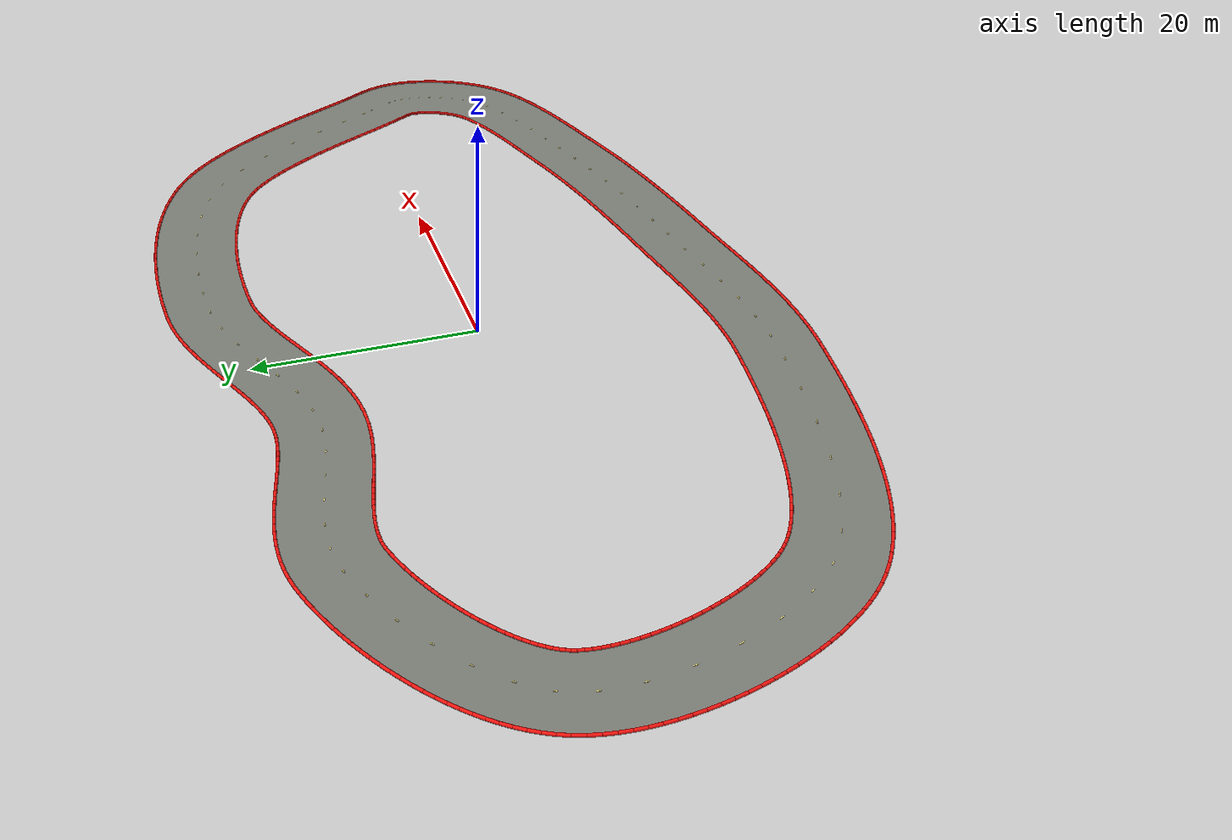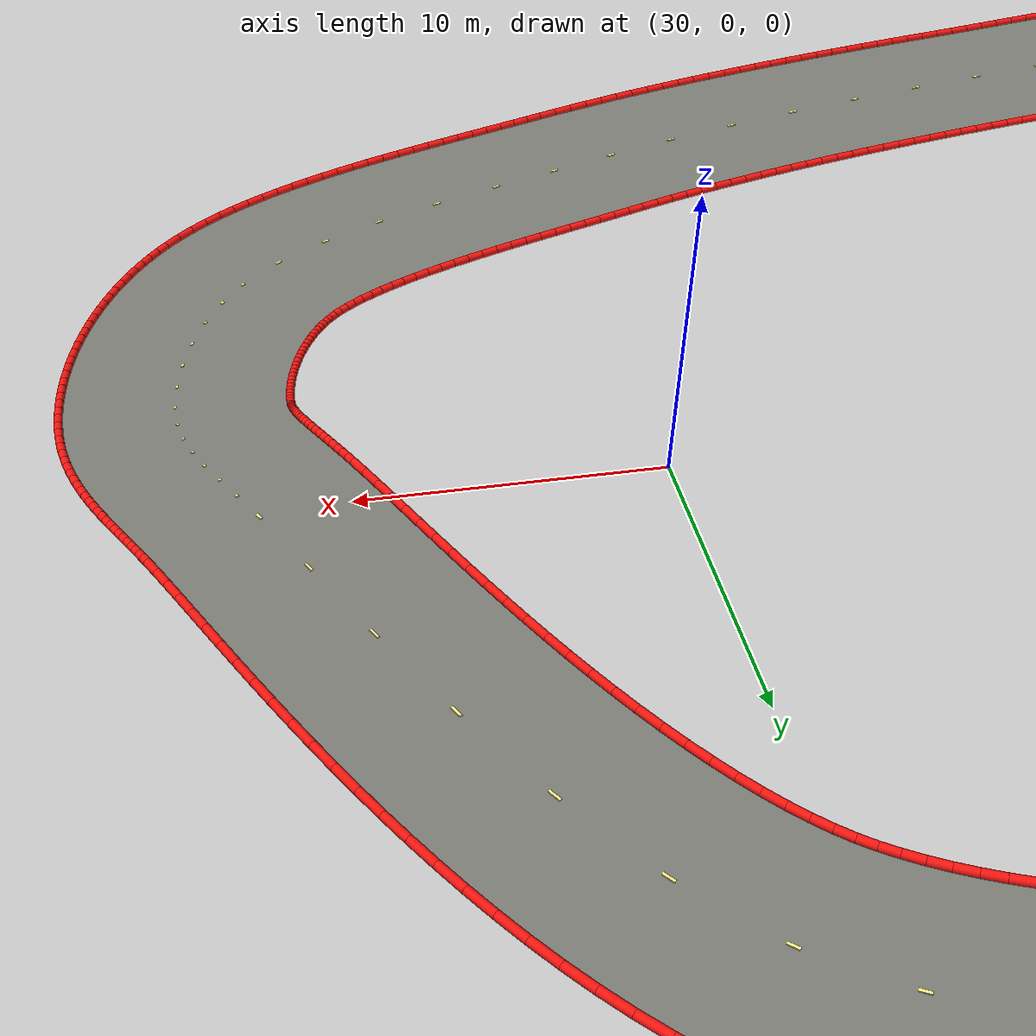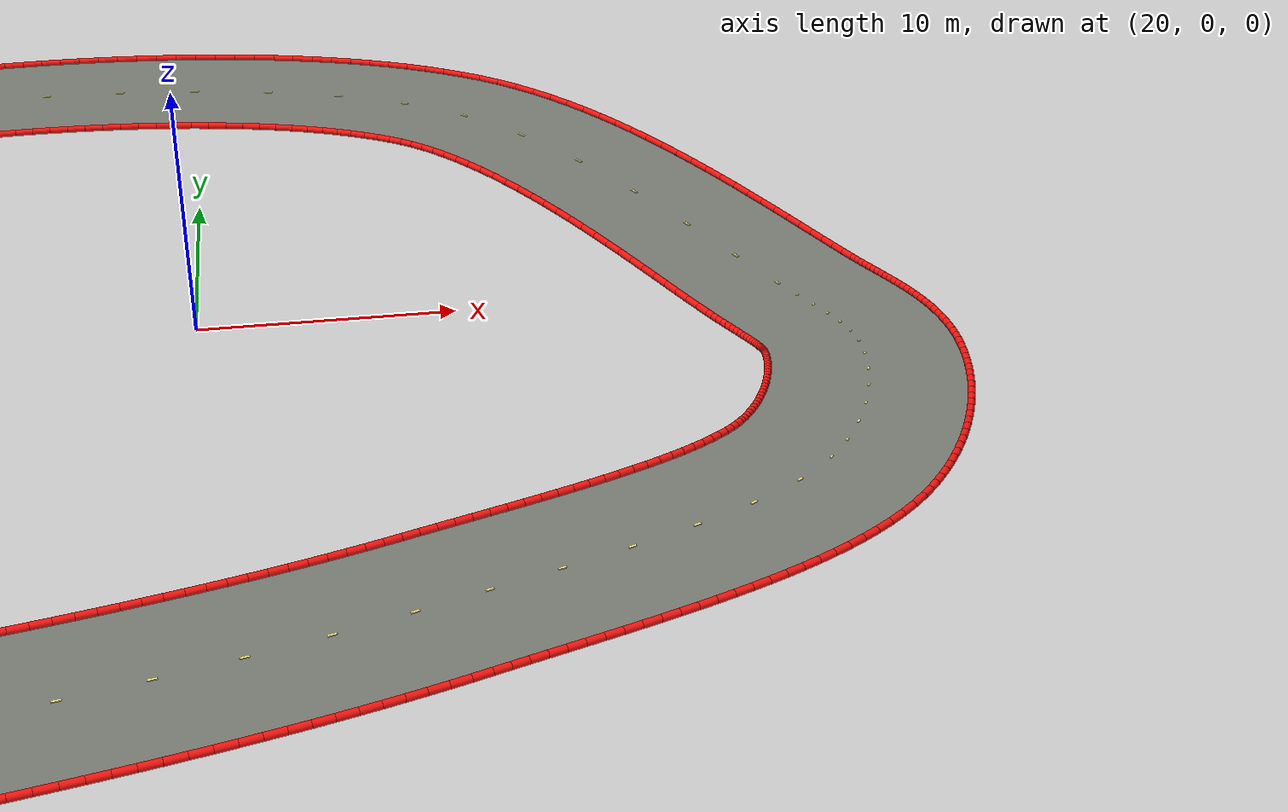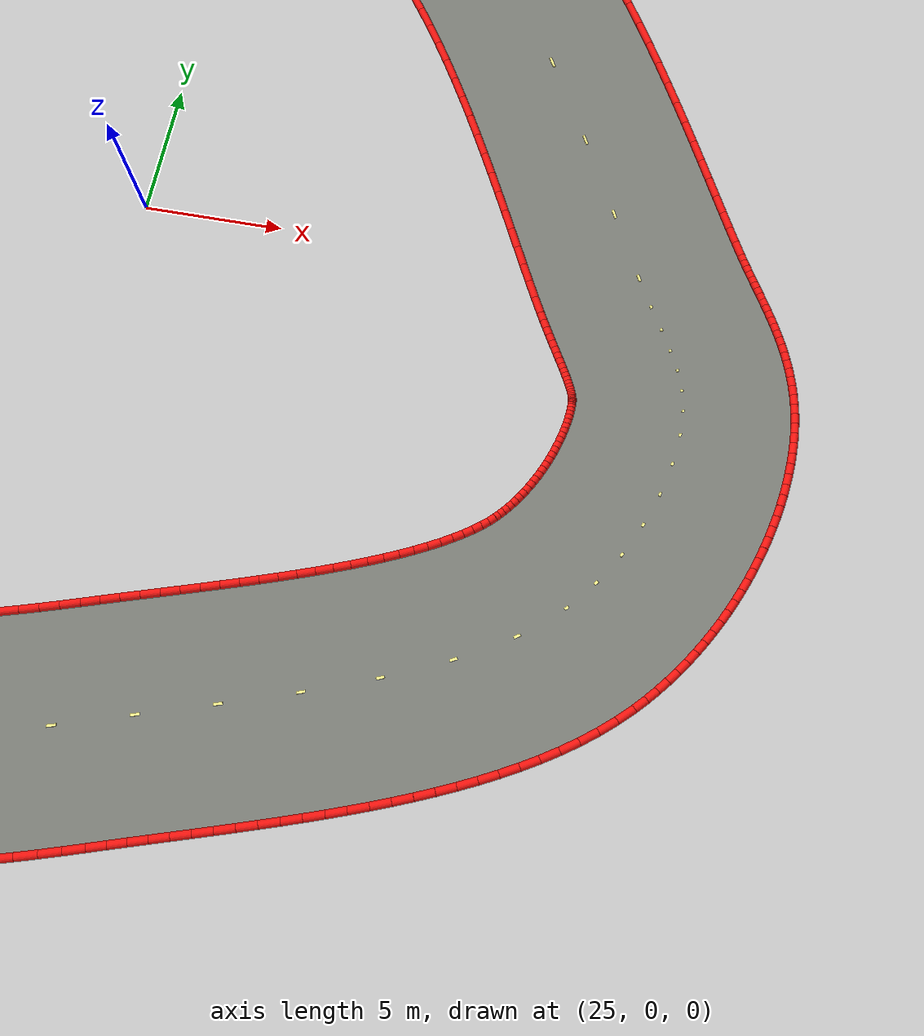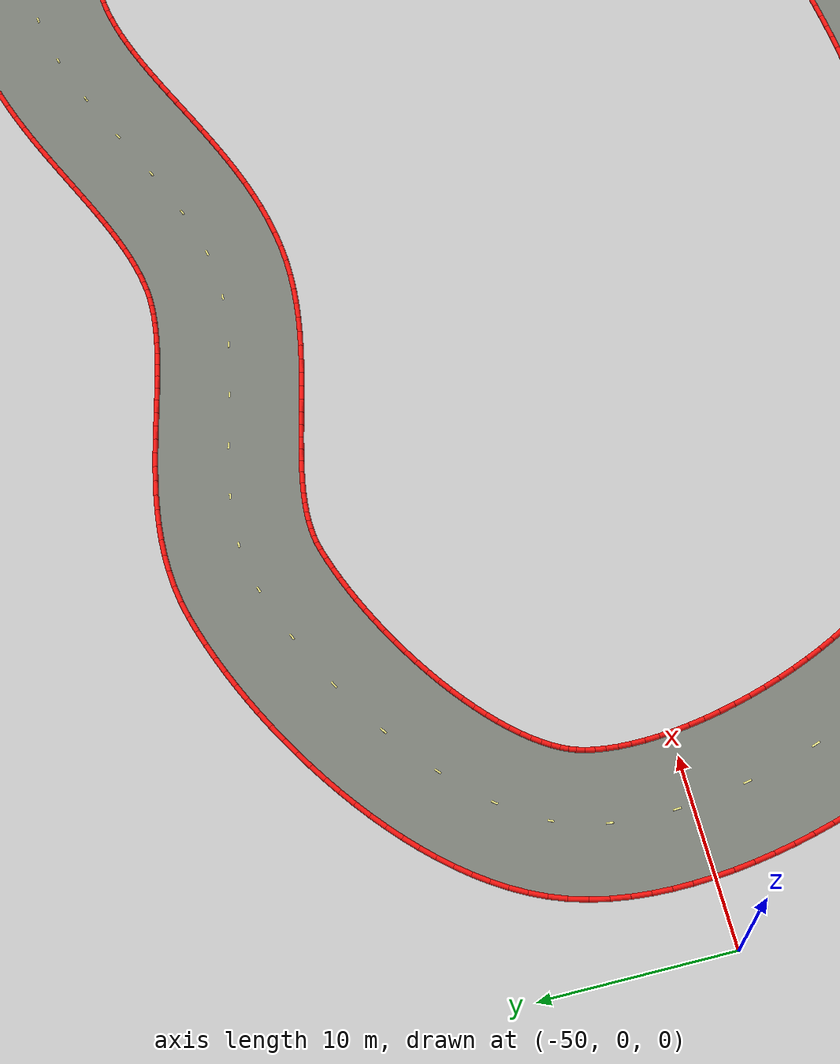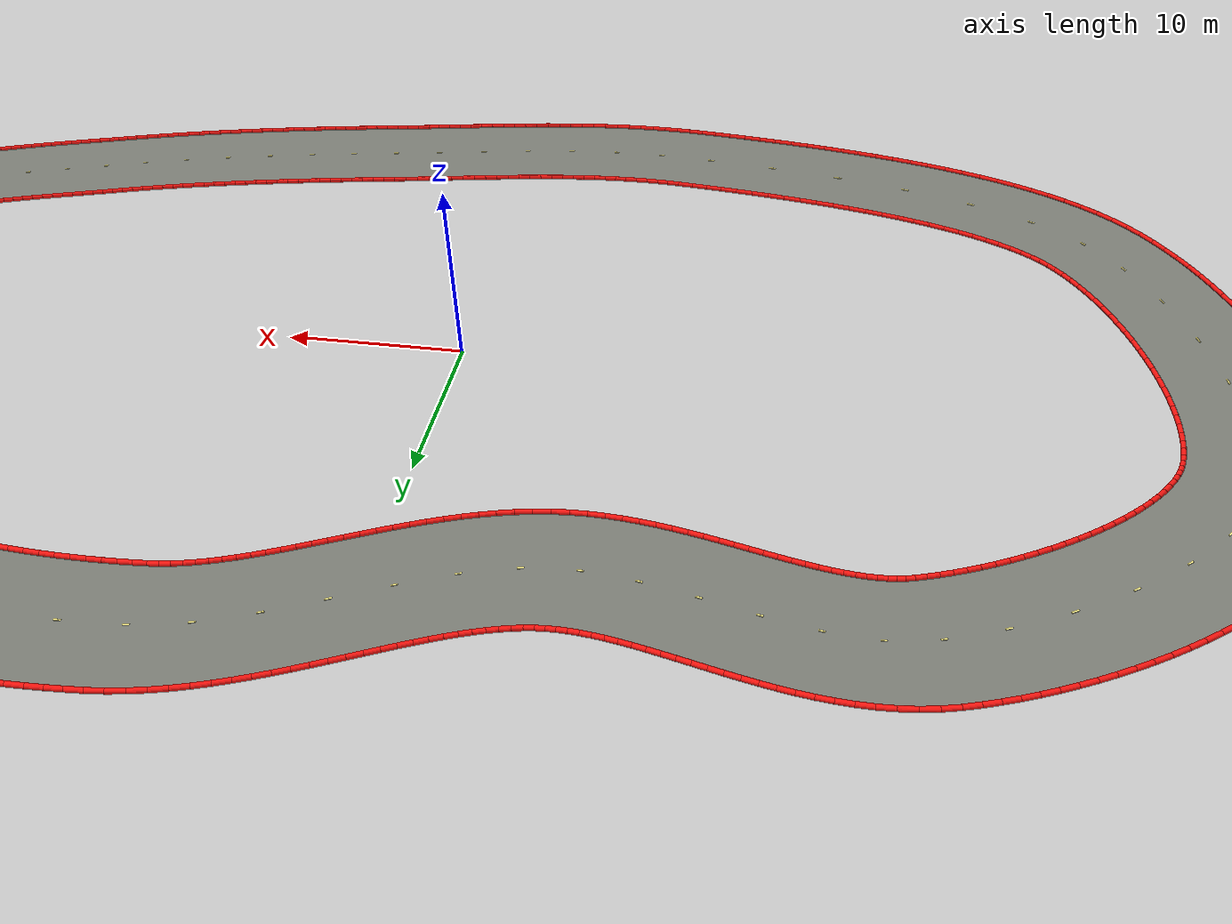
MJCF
<mujoco model="mini_monaco_track_visuals">
  <asset>
    <mesh name="track_surface_mesh" inertia="shell" vertex="39.67931 -1.74227 0.02200 39.39540 -1.19363 0.02200 39.09854 -0.60560 0.02200 38.79019 0.01462 0.02200 38.46925 0.66516 0.02200 38.13515 1.34338 0.02200 37.78764 2.04611 0.02200 37.42666 2.76987 0.02200 37.05236 3.51089 0.02200 36.66495 4.26526 0.02200 36.26479 5.02888 0.02200 35.85230 5.79756 0.02200 35.42802 6.56700 0.02200 34.99255 7.33282 0.02200 34.54664 8.09054 0.02200 34.09114 8.83562 0.02200 33.62705 9.56345 0.02200 33.15557 10.26935 0.02200 32.67810 10.94858 0.02200 32.19633 11.59638 0.02200 31.71226 12.20797 0.02200 31.22831 12.77865 0.02200 30.74737 13.30382 0.02200 30.27289 13.77916 0.02200 29.80892 14.20085 0.02200 29.36011 14.56579 0.02200 28.91214 14.88498 0.02200 28.42859 15.18840 0.02200 27.89715 15.48940 0.02200 27.33324 15.77767 0.02200 26.73857 16.05232 0.02200 26.11504 16.31262 0.02200 25.46470 16.55794 0.02200 24.78968 16.78781 0.02200 24.09219 17.00189 0.02200 23.37446 17.19994 0.02200 22.63876 17.38186 0.02200 21.88736 17.54761 0.02200 21.12252 17.69725 0.02200 20.34650 17.83092 0.02200 19.56154 17.94881 0.02200 18.76989 18.05115 0.02200 17.97375 18.13824 0.02200 17.17535 18.21042 0.02200 16.37688 18.26805 0.02200 15.58054 18.31153 0.02200 14.78852 18.34128 0.02200 14.00301 18.35776 0.02200 13.22619 18.36143 0.02200 12.46027 18.35280 0.02200 11.70747 18.33237 0.02200 10.97003 18.30070 0.02200 10.28593 18.26092 0.02200 9.72501 18.20878 0.02200 9.19145 18.13039 0.02200 8.64577 18.02358 0.02200 8.08722 17.88903 0.02200 7.51551 17.72770 0.02200 6.93068 17.54083 0.02200 6.33294 17.32996 0.02200 5.72262 17.09692 0.02200 5.10005 16.84380 0.02200 4.46548 16.57289 0.02200 3.81910 16.28669 0.02200 3.16096 15.98783 0.02200 2.49094 15.67907 0.02200 1.80879 15.36331 0.02200 1.11409 15.04353 0.02200 0.40624 14.72284 0.02200 -0.31549 14.40446 0.02200 -1.05203 14.09174 0.02200 -1.80440 13.78821 0.02200 -2.57376 13.49762 0.02200 -3.36132 13.22394 0.02200 -4.16827 12.97144 0.02200 -4.99572 12.74474 0.02200 -5.84453 12.54877 0.02200 -6.71518 12.38886 0.02200 -7.61173 12.27015 0.02200 -8.50993 12.20225 0.02200 -9.40247 12.18501 0.02200 -10.27761 12.21253 0.02200 -11.13457 12.27817 0.02200 -11.97320 12.37571 0.02200 -12.79369 12.49939 0.02200 -13.59641 12.64389 0.02200 -14.38173 12.80431 0.02200 -15.14997 12.97607 0.02200 -15.90128 13.15487 0.02200 -16.63561 13.33665 0.02200 -17.35270 13.51758 0.02200 -18.05207 13.69397 0.02200 -18.73296 13.86234 0.02200 -19.39440 14.01941 0.02200 -20.03516 14.16210 0.02200 -20.65380 14.28759 0.02200 -21.24873 14.39340 0.02200 -21.81825 14.47743 0.02200 -22.36066 14.53805 0.02200 -22.87448 14.57417 0.02200 -23.35863 14.58527 0.02200 -23.81279 14.57134 0.02200 -24.23769 14.53277 0.02200 -24.63550 14.47000 0.02200 -25.05059 14.37218 0.02200 -25.58076 14.21709 0.02200 -26.17629 14.02366 0.02200 -26.79552 13.80258 0.02200 -27.43365 13.55496 0.02200 -28.08620 13.28201 0.02200 -28.74891 12.98499 0.02200 -29.41769 12.66524 0.02200 -30.08862 12.32415 0.02200 -30.75783 11.96315 0.02200 -31.42155 11.58377 0.02200 -32.07605 11.18757 0.02200 -32.71766 10.77621 0.02200 -33.34271 10.35148 0.02200 -33.94759 9.91526 0.02200 -34.52867 9.46960 0.02200 -35.08239 9.01674 0.02200 -35.60523 8.55911 0.02200 -36.09375 8.09946 0.02200 -36.54464 7.64080 0.02200 -36.95481 7.18652 0.02200 -37.32147 6.74041 0.02200 -37.64233 6.30666 0.02200 -37.91577 5.88979 0.02200 -38.14114 5.49457 0.02200 -38.31904 5.12564 0.02200 -38.45335 4.78191 0.02200 -38.57490 4.37280 0.02200 -38.67956 3.89426 0.02200 -38.76244 3.34860 0.02200 -38.81907 2.74304 0.02200 -38.84652 2.08485 0.02200 -38.84304 1.38111 0.02200 -38.80772 0.63858 0.02200 -38.74028 -0.13631 0.02200 -38.64090 -0.93743 0.02200 -38.51009 -1.75895 0.02200 -38.34863 -2.59522 0.02200 -38.15750 -3.44080 0.02200 -37.93782 -4.29041 0.02200 -37.69089 -5.13884 0.02200 -37.41813 -5.98097 0.02200 -37.12108 -6.81176 0.02200 -36.80145 -7.62616 0.02200 -36.46111 -8.41915 0.02200 -36.10210 -9.18571 0.02200 -35.72675 -9.92077 0.02200 -35.33763 -10.61929 0.02200 -34.93773 -11.27618 0.02200 -34.53048 -11.88640 0.02200 -34.11990 -12.44500 0.02200 -33.71070 -12.94725 0.02200 -33.31707 -13.38000 0.02200 -32.86539 -13.81227 0.02200 -32.35927 -14.23084 0.02200 -31.78554 -14.64654 0.02200 -31.14662 -15.05581 0.02200 -30.44596 -15.45549 0.02200 -29.68773 -15.84303 0.02200 -28.87649 -16.21642 0.02200 -28.01701 -16.57418 0.02200 -27.11418 -16.91527 0.02200 -26.17288 -17.23906 0.02200 -25.19796 -17.54521 0.02200 -24.19422 -17.83363 0.02200 -23.16636 -18.10443 0.02200 -22.11903 -18.35791 0.02200 -21.05679 -18.59446 0.02200 -19.98413 -18.81459 0.02200 -18.90548 -19.01891 0.02200 -17.82518 -19.20806 0.02200 -16.74754 -19.38276 0.02200 -15.67679 -19.54377 0.02200 -14.61712 -19.69188 0.02200 -13.57265 -19.82792 0.02200 -12.54745 -19.95273 0.02200 -11.54551 -20.06718 0.02200 -10.57078 -20.17216 0.02200 -9.64640 -20.26671 0.02200 -8.91055 -20.33109 0.02200 -8.19514 -20.37608 0.02200 -7.48055 -20.40433 0.02200 -6.76633 -20.41662 0.02200 -6.05209 -20.41373 0.02200 -5.33746 -20.39642 0.02200 -4.62211 -20.36546 0.02200 -3.90574 -20.32162 0.02200 -3.18808 -20.26568 0.02200 -2.46887 -20.19845 0.02200 -1.74789 -20.12071 0.02200 -1.02493 -20.03329 0.02200 -0.29979 -19.93704 0.02200 0.42772 -19.83281 0.02200 1.15777 -19.72147 0.02200 1.89053 -19.60392 0.02200 2.62619 -19.48107 0.02200 3.36492 -19.35385 0.02200 4.10687 -19.22321 0.02200 4.85224 -19.09013 0.02200 5.60120 -18.95560 0.02200 6.35394 -18.82063 0.02200 7.11064 -18.68625 0.02200 7.87150 -18.55351 0.02200 8.63672 -18.42348 0.02200 9.39696 -18.29881 0.02200 10.10989 -18.18339 0.02200 10.81390 -18.06740 0.02200 11.51725 -17.94934 0.02200 12.21965 -17.82910 0.02200 12.92084 -17.70657 0.02200 13.62051 -17.58166 0.02200 14.31840 -17.45426 0.02200 15.01421 -17.32425 0.02200 15.70766 -17.19154 0.02200 16.39845 -17.05604 0.02200 17.08630 -16.91763 0.02200 17.77092 -16.77621 0.02200 18.45202 -16.63170 0.02200 19.12929 -16.48400 0.02200 19.80245 -16.33301 0.02200 20.47119 -16.17865 0.02200 21.13522 -16.02081 0.02200 21.79424 -15.85943 0.02200 22.44794 -15.69440 0.02200 23.09603 -15.52566 0.02200 23.73819 -15.35311 0.02200 24.37413 -15.17669 0.02200 25.00353 -14.99632 0.02200 25.62609 -14.81194 0.02200 26.24150 -14.62347 0.02200 26.86282 -14.42658 0.02200 27.45154 -14.23840 0.02200 28.05775 -14.04715 0.02200 28.66606 -13.85681 0.02200 29.27508 -13.66690 0.02200 29.88338 -13.47698 0.02200 30.48943 -13.28665 0.02200 31.09168 -13.09555 0.02200 31.68851 -12.90336 0.02200 32.27826 -12.70979 0.02200 32.85919 -12.51460 0.02200 33.42955 -12.31760 0.02200 33.98748 -12.11865 0.02200 34.53112 -11.91769 0.02200 35.05850 -11.71471 0.02200 35.56761 -11.50983 0.02200 36.05637 -11.30326 0.02200 36.52263 -11.09538 0.02200 36.96419 -10.88672 0.02200 37.37878 -10.67805 0.02200 37.76412 -10.47039 0.02200 38.11793 -10.26510 0.02200 38.43798 -10.06390 0.02200 38.72222 -9.86898 0.02200 38.96893 -9.68302 0.02200 39.17687 -9.50917 0.02200 39.36507 -9.33173 0.02200 39.47511 -9.21681 0.02200 39.59968 -9.07789 0.02200 39.72221 -8.93135 0.02200 39.84225 -8.77757 0.02200 39.95941 -8.61702 0.02200 40.07327 -8.45022 0.02200 40.18344 -8.27772 0.02200 40.28954 -8.10015 0.02200 40.39124 -7.91816 0.02200 40.48822 -7.73244 0.02200 40.58016 -7.54372 0.02200 40.66682 -7.35277 0.02200 40.74795 -7.16038 0.02200 40.82333 -6.96737 0.02200 40.89278 -6.77460 0.02200 40.95614 -6.58295 0.02200 41.01331 -6.39336 0.02200 41.06418 -6.20678 0.02200 41.10871 -6.02422 0.02200 41.14690 -5.84673 0.02200 41.17879 -5.67542 0.02200 41.20448 -5.51146 0.02200 41.22416 -5.35610 0.02200 41.23808 -5.21065 0.02200 41.24661 -5.07653 0.02200 41.25023 -4.95882 0.02200 41.24989 -4.90007 0.02200 41.24771 -4.85425 0.02200 41.24417 -4.81474 0.02200 41.23943 -4.77886 0.02200 41.23332 -4.74388 0.02200 41.22534 -4.70714 0.02200 41.21475 -4.66616 0.02200 41.20058 -4.61872 0.02200 41.18180 -4.56295 0.02200 41.15731 -4.49734 0.02200 41.12613 -4.42073 0.02200 41.08738 -4.33227 0.02200 41.04038 -4.23141 0.02200 40.98463 -4.11780 0.02200 40.91984 -3.99125 0.02200 40.84593 -3.85169 0.02200 40.76299 -3.69913 0.02200 40.67125 -3.53358 0.02200 40.57109 -3.35510 0.02200 40.46297 -3.16374 0.02200 40.34744 -2.95952 0.02200 40.22510 -2.74245 0.02200 40.09660 -2.51252 0.02200 39.96260 -2.26969 0.02200 39.82377 -2.01390 0.02200 46.32069 1.74227 0.02200 46.07371 2.21962 0.02200 45.80418 2.75364 0.02200 45.51116 3.34308 0.02200 45.19625 3.98142 0.02200 44.86055 4.66286 0.02200 44.50484 5.38216 0.02200 44.12965 6.13438 0.02200 43.73540 6.91485 0.02200 43.32235 7.71910 0.02200 42.89069 8.54278 0.02200 42.44049 9.38167 0.02200 41.97174 10.23165 0.02200 41.48435 11.08869 0.02200 40.97809 11.94883 0.02200 40.45263 12.80821 0.02200 39.90746 13.66301 0.02200 39.34193 14.50950 0.02200 38.75513 15.34399 0.02200 38.14591 16.16282 0.02200 37.51276 16.96235 0.02200 36.85379 17.73888 0.02200 36.16662 18.48857 0.02200 35.44832 19.20732 0.02200 34.69536 19.89055 0.02200 33.90359 20.53292 0.02200 33.08786 21.11502 0.02200 32.27486 21.62705 0.02200 31.45422 22.09222 0.02200 30.61427 22.52191 0.02200 29.75705 22.91809 0.02200 28.88442 23.28260 0.02200 27.99808 23.61712 0.02200 27.09966 23.92322 0.02200 26.19069 24.20232 0.02200 25.27270 24.45575 0.02200 24.34717 24.68469 0.02200 23.41559 24.89026 0.02200 22.47945 25.07348 0.02200 21.54025 25.23531 0.02200 20.59948 25.37664 0.02200 19.65868 25.49830 0.02200 18.71936 25.60109 0.02200 17.78308 25.68576 0.02200 16.85138 25.75303 0.02200 15.92583 25.80358 0.02200 15.00798 25.83807 0.02200 14.09941 25.85714 0.02200 13.20167 25.86139 0.02200 12.31631 25.85141 0.02200 11.44487 25.82777 0.02200 10.58888 25.79101 0.02200 9.71407 25.73908 0.02200 8.82944 25.65511 0.02200 7.92821 25.52324 0.02200 7.04914 25.35166 0.02200 6.19224 25.14569 0.02200 5.35707 24.91040 0.02200 4.54284 24.65056 0.02200 3.74860 24.37064 0.02200 2.97329 24.07483 0.02200 2.21586 23.76705 0.02200 1.47528 23.45102 0.02200 0.75066 23.13028 0.02200 0.04121 22.80818 0.02200 -0.65370 22.48798 0.02200 -1.33456 22.17282 0.02200 -2.00168 21.86570 0.02200 -2.65521 21.56956 0.02200 -3.29513 21.28717 0.02200 -3.92127 21.02120 0.02200 -4.53333 20.77412 0.02200 -5.13091 20.54823 0.02200 -5.71352 20.34554 0.02200 -6.28070 20.16781 0.02200 -6.83211 20.01644 0.02200 -7.36759 19.89249 0.02200 -7.88742 19.79668 0.02200 -8.38827 19.72985 0.02200 -8.86398 19.69389 0.02200 -9.35471 19.68485 0.02200 -9.87115 19.70151 0.02200 -10.41300 19.74338 0.02200 -10.97935 19.80957 0.02200 -11.56895 19.89871 0.02200 -12.18038 20.00901 0.02200 -12.81217 20.13824 0.02200 -13.46298 20.28388 0.02200 -14.13157 20.44309 0.02200 -14.81693 20.61281 0.02200 -15.51826 20.78977 0.02200 -16.23498 20.97052 0.02200 -16.96677 21.15141 0.02200 -17.71357 21.32864 0.02200 -18.47552 21.49814 0.02200 -19.25299 21.65561 0.02200 -20.04653 21.79642 0.02200 -20.85677 21.91554 0.02200 -21.68434 22.00749 0.02200 -22.52966 22.06624 0.02200 -23.39274 22.08519 0.02200 -24.27285 22.05722 0.02200 -25.16818 21.97483 0.02200 -26.07552 21.83045 0.02200 -26.94941 21.62782 0.02200 -27.78600 21.38556 0.02200 -28.59530 21.12284 0.02200 -29.41285 20.83107 0.02200 -30.23732 20.51121 0.02200 -31.06709 20.16418 0.02200 -31.90029 19.79078 0.02200 -32.73489 19.39177 0.02200 -33.56871 18.96786 0.02200 -34.39949 18.51970 0.02200 -35.22487 18.04788 0.02200 -36.04247 17.55290 0.02200 -36.84986 17.03520 0.02200 -37.64456 16.49511 0.02200 -38.42409 15.93281 0.02200 -39.18595 15.34836 0.02200 -39.92757 14.74161 0.02200 -40.64637 14.11221 0.02200 -41.33966 13.45953 0.02200 -42.00464 12.78263 0.02200 -42.63828 12.08021 0.02200 -43.23724 11.35058 0.02200 -43.79771 10.59166 0.02200 -44.31518 9.80100 0.02200 -44.78419 8.97593 0.02200 -45.19801 8.11389 0.02200 -45.54665 7.21809 0.02200 -45.83557 6.25232 0.02200 -46.05299 5.26636 0.02200 -46.20613 4.26593 0.02200 -46.30179 3.25185 0.02200 -46.34521 2.22485 0.02200 -46.34050 1.18591 0.02200 -46.29088 0.13627 0.02200 -46.19897 -0.92246 0.02200 -46.06690 -1.98837 0.02200 -45.89651 -3.05929 0.02200 -45.68933 -4.13282 0.02200 -45.44672 -5.20636 0.02200 -45.16988 -6.27721 0.02200 -44.85984 -7.34251 0.02200 -44.51753 -8.39936 0.02200 -44.14370 -9.44478 0.02200 -43.73900 -10.47579 0.02200 -43.30389 -11.48938 0.02200 -42.83863 -12.48255 0.02200 -42.34325 -13.45232 0.02200 -41.81748 -14.39574 0.02200 -41.26068 -15.30983 0.02200 -40.67174 -16.19163 0.02200 -40.04897 -17.03805 0.02200 -39.38998 -17.84580 0.02200 -38.68293 -18.62000 0.02200 -37.85243 -19.41401 0.02200 -36.95546 -20.15748 0.02200 -36.01314 -20.84149 0.02200 -35.03099 -21.47154 0.02200 -34.01346 -22.05269 0.02200 -32.96434 -22.58943 0.02200 -31.88701 -23.08568 0.02200 -30.78462 -23.54486 0.02200 -29.66022 -23.96989 0.02200 -28.51686 -24.36337 0.02200 -27.35764 -24.72753 0.02200 -26.18568 -25.06440 0.02200 -25.00421 -25.37577 0.02200 -23.81653 -25.66328 0.02200 -22.62601 -25.92846 0.02200 -21.43608 -26.17271 0.02200 -20.25027 -26.39736 0.02200 -19.07215 -26.60367 0.02200 -17.90536 -26.79285 0.02200 -16.75360 -26.96607 0.02200 -15.62062 -27.12444 0.02200 -14.51022 -27.26908 0.02200 -13.42629 -27.40106 0.02200 -12.37274 -27.52142 0.02200 -11.35358 -27.63120 0.02200 -10.35360 -27.73329 0.02200 -9.47201 -27.81004 0.02200 -8.57886 -27.86625 0.02200 -7.69345 -27.90130 0.02200 -6.81591 -27.91645 0.02200 -5.94632 -27.91298 0.02200 -5.08471 -27.89216 0.02200 -4.23110 -27.85526 0.02200 -3.38548 -27.80355 0.02200 -2.54779 -27.73830 0.02200 -1.71796 -27.66076 0.02200 -0.89589 -27.57216 0.02200 -0.08149 -27.47372 0.02200 0.72537 -27.36665 0.02200 1.52484 -27.25213 0.02200 2.31704 -27.13133 0.02200 3.10213 -27.00541 0.02200 3.88026 -26.87548 0.02200 4.65156 -26.74266 0.02200 5.41620 -26.60804 0.02200 6.17431 -26.47269 0.02200 6.92604 -26.33766 0.02200 7.67152 -26.20399 0.02200 8.41088 -26.07268 0.02200 9.14425 -25.94472 0.02200 9.87175 -25.82109 0.02200 10.60304 -25.70119 0.02200 11.31881 -25.58532 0.02200 12.04432 -25.46578 0.02200 12.77076 -25.34384 0.02200 13.49787 -25.21937 0.02200 14.22539 -25.09225 0.02200 14.95306 -24.96234 0.02200 15.68062 -24.82951 0.02200 16.40781 -24.69364 0.02200 17.13438 -24.55459 0.02200 17.86008 -24.41223 0.02200 18.58464 -24.26643 0.02200 19.30783 -24.11705 0.02200 20.02939 -23.96395 0.02200 20.74908 -23.80700 0.02200 21.46664 -23.64605 0.02200 22.18183 -23.48096 0.02200 22.89441 -23.31158 0.02200 23.60413 -23.13777 0.02200 24.31076 -22.95938 0.02200 25.01406 -22.77625 0.02200 25.71378 -22.58824 0.02200 26.40969 -22.39517 0.02200 27.10156 -22.19690 0.02200 27.78915 -21.99325 0.02200 28.47223 -21.78405 0.02200 29.13718 -21.57342 0.02200 29.72154 -21.38663 0.02200 30.30581 -21.20230 0.02200 30.90224 -21.01569 0.02200 31.50906 -20.82646 0.02200 32.12460 -20.63427 0.02200 32.74723 -20.43873 0.02200 33.37537 -20.23941 0.02200 34.00751 -20.03583 0.02200 34.64218 -19.82750 0.02200 35.27797 -19.61386 0.02200 35.91351 -19.39432 0.02200 36.54750 -19.16822 0.02200 37.17869 -18.93483 0.02200 37.80591 -18.69337 0.02200 38.42802 -18.44294 0.02200 39.04399 -18.18252 0.02200 39.65280 -17.91095 0.02200 40.25355 -17.62691 0.02200 40.84535 -17.32883 0.02200 41.42735 -17.01491 0.02200 41.99871 -16.68300 0.02200 42.55851 -16.33057 0.02200 43.10566 -15.95466 0.02200 43.63876 -15.55180 0.02200 44.15591 -15.11802 0.02200 44.63493 -14.66827 0.02200 44.96722 -14.32433 0.02200 45.26840 -13.98865 0.02200 45.55501 -13.64604 0.02200 45.82744 -13.29726 0.02200 46.08604 -12.94304 0.02200 46.33120 -12.58402 0.02200 46.56325 -12.22082 0.02200 46.78252 -11.85398 0.02200 46.98932 -11.48402 0.02200 47.18392 -11.11142 0.02200 47.36658 -10.73662 0.02200 47.53751 -10.36003 0.02200 47.69693 -9.98202 0.02200 47.84499 -9.60295 0.02200 47.98183 -9.22312 0.02200 48.10757 -8.84283 0.02200 48.22229 -8.46231 0.02200 48.32603 -8.08177 0.02200 48.41878 -7.70138 0.02200 48.50052 -7.32126 0.02200 48.57116 -6.94147 0.02200 48.63054 -6.56200 0.02200 48.67846 -6.18280 0.02200 48.71459 -5.80370 0.02200 48.73854 -5.42447 0.02200 48.74977 -5.04118 0.02200 48.74696 -4.69030 0.02200 48.72991 -4.33792 0.02200 48.69863 -3.98951 0.02200 48.65346 -3.64657 0.02200 48.59509 -3.31062 0.02200 48.52451 -2.98317 0.02200 48.44298 -2.66550 0.02200 48.35195 -2.35864 0.02200 48.25299 -2.06330 0.02200 48.14766 -1.77981 0.02200 48.03749 -1.50814 0.02200 47.92383 -1.24795 0.02200 47.80788 -0.99863 0.02200 47.69065 -0.75933 0.02200 47.57291 -0.52907 0.02200 47.45526 -0.30673 0.02200 47.33813 -0.09114 0.02200 47.22177 0.11892 0.02200 47.10632 0.32468 0.02200 46.99181 0.52736 0.02200 46.87821 0.72817 0.02200 46.76540 0.92831 0.02200 46.65326 1.12893 0.02200 46.54163 1.33119 0.02200 46.43034 1.53621 0.02200" face="0 313 1 0 312 313 1 314 2 1 313 314 2 315 3 2 314 315 3 316 4 3 315 316 4 317 5 4 316 317 5 318 6 5 317 318 6 319 7 6 318 319 7 320 8 7 319 320 8 321 9 8 320 321 9 322 10 9 321 322 10 323 11 10 322 323 11 324 12 11 323 324 12 325 13 12 324 325 13 326 14 13 325 326 14 327 15 14 326 327 15 328 16 15 327 328 16 329 17 16 328 329 17 330 18 17 329 330 18 331 19 18 330 331 19 332 20 19 331 332 20 333 21 20 332 333 21 334 22 21 333 334 22 335 23 22 334 335 23 336 24 23 335 336 24 337 25 24 336 337 25 338 26 25 337 338 26 339 27 26 338 339 27 340 28 27 339 340 28 341 29 28 340 341 29 342 30 29 341 342 30 343 31 30 342 343 31 344 32 31 343 344 32 345 33 32 344 345 33 346 34 33 345 346 34 347 35 34 346 347 35 348 36 35 347 348 36 349 37 36 348 349 37 350 38 37 349 350 38 351 39 38 350 351 39 352 40 39 351 352 40 353 41 40 352 353 41 354 42 41 353 354 42 355 43 42 354 355 43 356 44 43 355 356 44 357 45 44 356 357 45 358 46 45 357 358 46 359 47 46 358 359 47 360 48 47 359 360 48 361 49 48 360 361 49 362 50 49 361 362 50 363 51 50 362 363 51 364 52 51 363 364 52 365 53 52 364 365 53 366 54 53 365 366 54 367 55 54 366 367 55 368 56 55 367 368 56 369 57 56 368 369 57 370 58 57 369 370 58 371 59 58 370 371 59 372 60 59 371 372 60 373 61 60 372 373 61 374 62 61 373 374 62 375 63 62 374 375 63 376 64 63 375 376 64 377 65 64 376 377 65 378 66 65 377 378 66 379 67 66 378 379 67 380 68 67 379 380 68 381 69 68 380 381 69 382 70 69 381 382 70 383 71 70 382 383 71 384 72 71 383 384 72 385 73 72 384 385 73 386 74 73 385 386 74 387 75 74 386 387 75 388 76 75 387 388 76 389 77 76 388 389 77 390 78 77 389 390 78 391 79 78 390 391 79 392 80 79 391 392 80 393 81 80 392 393 81 394 82 81 393 394 82 395 83 82 394 395 83 396 84 83 395 396 84 397 85 84 396 397 85 398 86 85 397 398 86 399 87 86 398 399 87 400 88 87 399 400 88 401 89 88 400 401 89 402 90 89 401 402 90 403 91 90 402 403 91 404 92 91 403 404 92 405 93 92 404 405 93 406 94 93 405 406 94 407 95 94 406 407 95 408 96 95 407 408 96 409 97 96 408 409 97 410 98 97 409 410 98 411 99 98 410 411 99 412 100 99 411 412 100 413 101 100 412 413 101 414 102 101 413 414 102 415 103 102 414 415 103 416 104 103 415 416 104 417 105 104 416 417 105 418 106 105 417 418 106 419 107 106 418 419 107 420 108 107 419 420 108 421 109 108 420 421 109 422 110 109 421 422 110 423 111 110 422 423 111 424 112 111 423 424 112 425 113 112 424 425 113 426 114 113 425 426 114 427 115 114 426 427 115 428 116 115 427 428 116 429 117 116 428 429 117 430 118 117 429 430 118 431 119 118 430 431 119 432 120 119 431 432 120 433 121 120 432 433 121 434 122 121 433 434 122 435 123 122 434 435 123 436 124 123 435 436 124 437 125 124 436 437 125 438 126 125 437 438 126 439 127 126 438 439 127 440 128 127 439 440 128 441 129 128 440 441 129 442 130 129 441 442 130 443 131 130 442 443 131 444 132 131 443 444 132 445 133 132 444 445 133 446 134 133 445 446 134 447 135 134 446 447 135 448 136 135 447 448 136 449 137 136 448 449 137 450 138 137 449 450 138 451 139 138 450 451 139 452 140 139 451 452 140 453 141 140 452 453 141 454 142 141 453 454 142 455 143 142 454 455 143 456 144 143 455 456 144 457 145 144 456 457 145 458 146 145 457 458 146 459 147 146 458 459 147 460 148 147 459 460 148 461 149 148 460 461 149 462 150 149 461 462 150 463 151 150 462 463 151 464 152 151 463 464 152 465 153 152 464 465 153 466 154 153 465 466 154 467 155 154 466 467 155 468 156 155 467 468 156 469 157 156 468 469 157 470 158 157 469 470 158 471 159 158 470 471 159 472 160 159 471 472 160 473 161 160 472 473 161 474 162 161 473 474 162 475 163 162 474 475 163 476 164 163 475 476 164 477 165 164 476 477 165 478 166 165 477 478 166 479 167 166 478 479 167 480 168 167 479 480 168 481 169 168 480 481 169 482 170 169 481 482 170 483 171 170 482 483 171 484 172 171 483 484 172 485 173 172 484 485 173 486 174 173 485 486 174 487 175 174 486 487 175 488 176 175 487 488 176 489 177 176 488 489 177 490 178 177 489 490 178 491 179 178 490 491 179 492 180 179 491 492 180 493 181 180 492 493 181 494 182 181 493 494 182 495 183 182 494 495 183 496 184 183 495 496 184 497 185 184 496 497 185 498 186 185 497 498 186 499 187 186 498 499 187 500 188 187 499 500 188 501 189 188 500 501 189 502 190 189 501 502 190 503 191 190 502 503 191 504 192 191 503 504 192 505 193 192 504 505 193 506 194 193 505 506 194 507 195 194 506 507 195 508 196 195 507 508 196 509 197 196 508 509 197 510 198 197 509 510 198 511 199 198 510 511 199 512 200 199 511 512 200 513 201 200 512 513 201 514 202 201 513 514 202 515 203 202 514 515 203 516 204 203 515 516 204 517 205 204 516 517 205 518 206 205 517 518 206 519 207 206 518 519 207 520 208 207 519 520 208 521 209 208 520 521 209 522 210 209 521 522 210 523 211 210 522 523 211 524 212 211 523 524 212 525 213 212 524 525 213 526 214 213 525 526 214 527 215 214 526 527 215 528 216 215 527 528 216 529 217 216 528 529 217 530 218 217 529 530 218 531 219 218 530 531 219 532 220 219 531 532 220 533 221 220 532 533 221 534 222 221 533 534 222 535 223 222 534 535 223 536 224 223 535 536 224 537 225 224 536 537 225 538 226 225 537 538 226 539 227 226 538 539 227 540 228 227 539 540 228 541 229 228 540 541 229 542 230 229 541 542 230 543 231 230 542 543 231 544 232 231 543 544 232 545 233 232 544 545 233 546 234 233 545 546 234 547 235 234 546 547 235 548 236 235 547 548 236 549 237 236 548 549 237 550 238 237 549 550 238 551 239 238 550 551 239 552 240 239 551 552 240 553 241 240 552 553 241 554 242 241 553 554 242 555 243 242 554 555 243 556 244 243 555 556 244 557 245 244 556 557 245 558 246 245 557 558 246 559 247 246 558 559 247 560 248 247 559 560 248 561 249 248 560 561 249 562 250 249 561 562 250 563 251 250 562 563 251 564 252 251 563 564 252 565 253 252 564 565 253 566 254 253 565 566 254 567 255 254 566 567 255 568 256 255 567 568 256 569 257 256 568 569 257 570 258 257 569 570 258 571 259 258 570 571 259 572 260 259 571 572 260 573 261 260 572 573 261 574 262 261 573 574 262 575 263 262 574 575 263 576 264 263 575 576 264 577 265 264 576 577 265 578 266 265 577 578 266 579 267 266 578 579 267 580 268 267 579 580 268 581 269 268 580 581 269 582 270 269 581 582 270 583 271 270 582 583 271 584 272 271 583 584 272 585 273 272 584 585 273 586 274 273 585 586 274 587 275 274 586 587 275 588 276 275 587 588 276 589 277 276 588 589 277 590 278 277 589 590 278 591 279 278 590 591 279 592 280 279 591 592 280 593 281 280 592 593 281 594 282 281 593 594 282 595 283 282 594 595 283 596 284 283 595 596 284 597 285 284 596 597 285 598 286 285 597 598 286 599 287 286 598 599 287 600 288 287 599 600 288 601 289 288 600 601 289 602 290 289 601 602 290 603 291 290 602 603 291 604 292 291 603 604 292 605 293 292 604 605 293 606 294 293 605 606 294 607 295 294 606 607 295 608 296 295 607 608 296 609 297 296 608 609 297 610 298 297 609 610 298 611 299 298 610 611 299 612 300 299 611 612 300 613 301 300 612 613 301 614 302 301 613 614 302 615 303 302 614 615 303 616 304 303 615 616 304 617 305 304 616 617 305 618 306 305 617 618 306 619 307 306 618 619 307 620 308 307 619 620 308 621 309 308 620 621 309 622 310 309 621 622 310 623 311 310 622 623 311 312 0 311 623 312"/>
    <material name="track_asphalt" rgba="0.48 0.49 0.46 1" emission="0.08"/>
    <material name="track_boundary" rgba="0.95 0.08 0.06 1" emission="0.05"/>
    <material name="track_centerline" rgba="1.0 0.95 0.55 1" emission="0.15"/>
  </asset>
  <worldbody>
    <geom name="track_surface" type="mesh" mesh="track_surface_mesh" material="track_asphalt" contype="0" conaffinity="0"/>
    <geom name="track_left_boundary_000" type="capsule" fromto="39.67931 -1.74227 0.09 39.39540 -1.19363 0.09" size="0.14" material="track_boundary" contype="0" conaffinity="0"/>
    <geom name="track_left_boundary_001" type="capsule" fromto="39.39540 -1.19363 0.09 39.09854 -0.60560 0.09" size="0.14" material="track_boundary" contype="0" conaffinity="0"/>
    <geom name="track_left_boundary_002" type="capsule" fromto="39.09854 -0.60560 0.09 38.79019 0.01462 0.09" size="0.14" material="track_boundary" contype="0" conaffinity="0"/>
    <geom name="track_left_boundary_003" type="capsule" fromto="38.79019 0.01462 0.09 38.46925 0.66516 0.09" size="0.14" material="track_boundary" contype="0" conaffinity="0"/>
    <geom name="track_left_boundary_004" type="capsule" fromto="38.46925 0.66516 0.09 38.13515 1.34338 0.09" size="0.14" material="track_boundary" contype="0" conaffinity="0"/>
    <geom name="track_left_boundary_005" type="capsule" fromto="38.13515 1.34338 0.09 37.78764 2.04611 0.09" size="0.14" material="track_boundary" contype="0" conaffinity="0"/>
    <geom name="track_left_boundary_006" type="capsule" fromto="37.78764 2.04611 0.09 37.42666 2.76987 0.09" size="0.14" material="track_boundary" contype="0" conaffinity="0"/>
    <geom name="track_left_boundary_007" type="capsule" fromto="37.42666 2.76987 0.09 37.05236 3.51089 0.09" size="0.14" material="track_boundary" contype="0" conaffinity="0"/>
    <geom name="track_left_boundary_008" type="capsule" fromto="37.05236 3.51089 0.09 36.66495 4.26526 0.09" size="0.14" material="track_boundary" contype="0" conaffinity="0"/>
    <geom name="track_left_boundary_009" type="capsule" fromto="36.66495 4.26526 0.09 36.26479 5.02888 0.09" size="0.14" material="track_boundary" contype="0" conaffinity="0"/>
    <geom name="track_left_boundary_010" type="capsule" fromto="36.26479 5.02888 0.09 35.85230 5.79756 0.09" size="0.14" material="track_boundary" contype="0" conaffinity="0"/>
    <geom name="track_left_boundary_011" type="capsule" fromto="35.85230 5.79756 0.09 35.42802 6.56700 0.09" size="0.14" material="track_boundary" contype="0" conaffinity="0"/>
    <geom name="track_left_boundary_012" type="capsule" fromto="35.42802 6.56700 0.09 34.99255 7.33282 0.09" size="0.14" material="track_boundary" contype="0" conaffinity="0"/>
    <geom name="track_left_boundary_013" type="capsule" fromto="34.99255 7.33282 0.09 34.54664 8.09054 0.09" size="0.14" material="track_boundary" contype="0" conaffinity="0"/>
    <geom name="track_left_boundary_014" type="capsule" fromto="34.54664 8.09054 0.09 34.09114 8.83562 0.09" size="0.14" material="track_boundary" contype="0" conaffinity="0"/>
    <geom name="track_left_boundary_015" type="capsule" fromto="34.09114 8.83562 0.09 33.62705 9.56345 0.09" size="0.14" material="track_boundary" contype="0" conaffinity="0"/>
    <geom name="track_left_boundary_016" type="capsule" fromto="33.62705 9.56345 0.09 33.15557 10.26935 0.09" size="0.14" material="track_boundary" contype="0" conaffinity="0"/>
    <geom name="track_left_boundary_017" type="capsule" fromto="33.15557 10.26935 0.09 32.67810 10.94858 0.09" size="0.14" material="track_boundary" contype="0" conaffinity="0"/>
    <geom name="track_left_boundary_018" type="capsule" fromto="32.67810 10.94858 0.09 32.19633 11.59638 0.09" size="0.14" material="track_boundary" contype="0" conaffinity="0"/>
    <geom name="track_left_boundary_019" type="capsule" fromto="32.19633 11.59638 0.09 31.71226 12.20797 0.09" size="0.14" material="track_boundary" contype="0" conaffinity="0"/>
    <geom name="track_left_boundary_020" type="capsule" fromto="31.71226 12.20797 0.09 31.22831 12.77865 0.09" size="0.14" material="track_boundary" contype="0" conaffinity="0"/>
    <geom name="track_left_boundary_021" type="capsule" fromto="31.22831 12.77865 0.09 30.74737 13.30382 0.09" size="0.14" material="track_boundary" contype="0" conaffinity="0"/>
    <geom name="track_left_boundary_022" type="capsule" fromto="30.74737 13.30382 0.09 30.27289 13.77916 0.09" size="0.14" material="track_boundary" contype="0" conaffinity="0"/>
    <geom name="track_left_boundary_023" type="capsule" fromto="30.27289 13.77916 0.09 29.80892 14.20085 0.09" size="0.14" material="track_boundary" contype="0" conaffinity="0"/>
    <geom name="track_left_boundary_024" type="capsule" fromto="29.80892 14.20085 0.09 29.36011 14.56579 0.09" size="0.14" material="track_boundary" contype="0" conaffinity="0"/>
    <geom name="track_left_boundary_025" type="capsule" fromto="29.36011 14.56579 0.09 28.91214 14.88498 0.09" size="0.14" material="track_boundary" contype="0" conaffinity="0"/>
    <geom name="track_left_boundary_026" type="capsule" fromto="28.91214 14.88498 0.09 28.42859 15.18840 0.09" size="0.14" material="track_boundary" contype="0" conaffinity="0"/>
    <geom name="track_left_boundary_027" type="capsule" fromto="28.42859 15.18840 0.09 27.89715 15.48940 0.09" size="0.14" material="track_boundary" contype="0" conaffinity="0"/>
    <geom name="track_left_boundary_028" type="capsule" fromto="27.89715 15.48940 0.09 27.33324 15.77767 0.09" size="0.14" material="track_boundary" contype="0" conaffinity="0"/>
    <geom name="track_left_boundary_029" type="capsule" fromto="27.33324 15.77767 0.09 26.73857 16.05232 0.09" size="0.14" material="track_boundary" contype="0" conaffinity="0"/>
    <geom name="track_left_boundary_030" type="capsule" fromto="26.73857 16.05232 0.09 26.11504 16.31262 0.09" size="0.14" material="track_boundary" contype="0" conaffinity="0"/>
    <geom name="track_left_boundary_031" type="capsule" fromto="26.11504 16.31262 0.09 25.46470 16.55794 0.09" size="0.14" material="track_boundary" contype="0" conaffinity="0"/>
    <geom name="track_left_boundary_032" type="capsule" fromto="25.46470 16.55794 0.09 24.78968 16.78781 0.09" size="0.14" material="track_boundary" contype="0" conaffinity="0"/>
    <geom name="track_left_boundary_033" type="capsule" fromto="24.78968 16.78781 0.09 24.09219 17.00189 0.09" size="0.14" material="track_boundary" contype="0" conaffinity="0"/>
    <geom name="track_left_boundary_034" type="capsule" fromto="24.09219 17.00189 0.09 23.37446 17.19994 0.09" size="0.14" material="track_boundary" contype="0" conaffinity="0"/>
    <geom name="track_left_boundary_035" type="capsule" fromto="23.37446 17.19994 0.09 22.63876 17.38186 0.09" size="0.14" material="track_boundary" contype="0" conaffinity="0"/>
    <geom name="track_left_boundary_036" type="capsule" fromto="22.63876 17.38186 0.09 21.88736 17.54761 0.09" size="0.14" material="track_boundary" contype="0" conaffinity="0"/>
    <geom name="track_left_boundary_037" type="capsule" fromto="21.88736 17.54761 0.09 21.12252 17.69725 0.09" size="0.14" material="track_boundary" contype="0" conaffinity="0"/>
    <geom name="track_left_boundary_038" type="capsule" fromto="21.12252 17.69725 0.09 20.34650 17.83092 0.09" size="0.14" material="track_boundary" contype="0" conaffinity="0"/>
    <geom name="track_left_boundary_039" type="capsule" fromto="20.34650 17.83092 0.09 19.56154 17.94881 0.09" size="0.14" material="track_boundary" contype="0" conaffinity="0"/>
    <geom name="track_left_boundary_040" type="capsule" fromto="19.56154 17.94881 0.09 18.76989 18.05115 0.09" size="0.14" material="track_boundary" contype="0" conaffinity="0"/>
    <geom name="track_left_boundary_041" type="capsule" fromto="18.76989 18.05115 0.09 17.97375 18.13824 0.09" size="0.14" material="track_boundary" contype="0" conaffinity="0"/>
    <geom name="track_left_boundary_042" type="capsule" fromto="17.97375 18.13824 0.09 17.17535 18.21042 0.09" size="0.14" material="track_boundary" contype="0" conaffinity="0"/>
    <geom name="track_left_boundary_043" type="capsule" fromto="17.17535 18.21042 0.09 16.37688 18.26805 0.09" size="0.14" material="track_boundary" contype="0" conaffinity="0"/>
    <geom name="track_left_boundary_044" type="capsule" fromto="16.37688 18.26805 0.09 15.58054 18.31153 0.09" size="0.14" material="track_boundary" contype="0" conaffinity="0"/>
    <geom name="track_left_boundary_045" type="capsule" fromto="15.58054 18.31153 0.09 14.78852 18.34128 0.09" size="0.14" material="track_boundary" contype="0" conaffinity="0"/>
    <geom name="track_left_boundary_046" type="capsule" fromto="14.78852 18.34128 0.09 14.00301 18.35776 0.09" size="0.14" material="track_boundary" contype="0" conaffinity="0"/>
    <geom name="track_left_boundary_047" type="capsule" fromto="14.00301 18.35776 0.09 13.22619 18.36143 0.09" size="0.14" material="track_boundary" contype="0" conaffinity="0"/>
    <geom name="track_left_boundary_048" type="capsule" fromto="13.22619 18.36143 0.09 12.46027 18.35280 0.09" size="0.14" material="track_boundary" contype="0" conaffinity="0"/>
    <geom name="track_left_boundary_049" type="capsule" fromto="12.46027 18.35280 0.09 11.70747 18.33237 0.09" size="0.14" material="track_boundary" contype="0" conaffinity="0"/>
    <geom name="track_left_boundary_050" type="capsule" fromto="11.70747 18.33237 0.09 10.97003 18.30070 0.09" size="0.14" material="track_boundary" contype="0" conaffinity="0"/>
    <geom name="track_left_boundary_051" type="capsule" fromto="10.97003 18.30070 0.09 10.28593 18.26092 0.09" size="0.14" material="track_boundary" contype="0" conaffinity="0"/>
    <geom name="track_left_boundary_052" type="capsule" fromto="10.28593 18.26092 0.09 9.72501 18.20878 0.09" size="0.14" material="track_boundary" contype="0" conaffinity="0"/>
    <geom name="track_left_boundary_053" type="capsule" fromto="9.72501 18.20878 0.09 9.19145 18.13039 0.09" size="0.14" material="track_boundary" contype="0" conaffinity="0"/>
    <geom name="track_left_boundary_054" type="capsule" fromto="9.19145 18.13039 0.09 8.64577 18.02358 0.09" size="0.14" material="track_boundary" contype="0" conaffinity="0"/>
    <geom name="track_left_boundary_055" type="capsule" fromto="8.64577 18.02358 0.09 8.08722 17.88903 0.09" size="0.14" material="track_boundary" contype="0" conaffinity="0"/>
    <geom name="track_left_boundary_056" type="capsule" fromto="8.08722 17.88903 0.09 7.51551 17.72770 0.09" size="0.14" material="track_boundary" contype="0" conaffinity="0"/>
    <geom name="track_left_boundary_057" type="capsule" fromto="7.51551 17.72770 0.09 6.93068 17.54083 0.09" size="0.14" material="track_boundary" contype="0" conaffinity="0"/>
    <geom name="track_left_boundary_058" type="capsule" fromto="6.93068 17.54083 0.09 6.33294 17.32996 0.09" size="0.14" material="track_boundary" contype="0" conaffinity="0"/>
    <geom name="track_left_boundary_059" type="capsule" fromto="6.33294 17.32996 0.09 5.72262 17.09692 0.09" size="0.14" material="track_boundary" contype="0" conaffinity="0"/>
    <geom name="track_left_boundary_060" type="capsule" fromto="5.72262 17.09692 0.09 5.10005 16.84380 0.09" size="0.14" material="track_boundary" contype="0" conaffinity="0"/>
    <geom name="track_left_boundary_061" type="capsule" fromto="5.10005 16.84380 0.09 4.46548 16.57289 0.09" size="0.14" material="track_boundary" contype="0" conaffinity="0"/>
    <geom name="track_left_boundary_062" type="capsule" fromto="4.46548 16.57289 0.09 3.81910 16.28669 0.09" size="0.14" material="track_boundary" contype="0" conaffinity="0"/>
    <geom name="track_left_boundary_063" type="capsule" fromto="3.81910 16.28669 0.09 3.16096 15.98783 0.09" size="0.14" material="track_boundary" contype="0" conaffinity="0"/>
    <geom name="track_left_boundary_064" type="capsule" fromto="3.16096 15.98783 0.09 2.49094 15.67907 0.09" size="0.14" material="track_boundary" contype="0" conaffinity="0"/>
    <geom name="track_left_boundary_065" type="capsule" fromto="2.49094 15.67907 0.09 1.80879 15.36331 0.09" size="0.14" material="track_boundary" contype="0" conaffinity="0"/>
    <geom name="track_left_boundary_066" type="capsule" fromto="1.80879 15.36331 0.09 1.11409 15.04353 0.09" size="0.14" material="track_boundary" contype="0" conaffinity="0"/>
    <geom name="track_left_boundary_067" type="capsule" fromto="1.11409 15.04353 0.09 0.40624 14.72284 0.09" size="0.14" material="track_boundary" contype="0" conaffinity="0"/>
    <geom name="track_left_boundary_068" type="capsule" fromto="0.40624 14.72284 0.09 -0.31549 14.40446 0.09" size="0.14" material="track_boundary" contype="0" conaffinity="0"/>
    <geom name="track_left_boundary_069" type="capsule" fromto="-0.31549 14.40446 0.09 -1.05203 14.09174 0.09" size="0.14" material="track_boundary" contype="0" conaffinity="0"/>
    <geom name="track_left_boundary_070" type="capsule" fromto="-1.05203 14.09174 0.09 -1.80440 13.78821 0.09" size="0.14" material="track_boundary" contype="0" conaffinity="0"/>
    <geom name="track_left_boundary_071" type="capsule" fromto="-1.80440 13.78821 0.09 -2.57376 13.49762 0.09" size="0.14" material="track_boundary" contype="0" conaffinity="0"/>
    <geom name="track_left_boundary_072" type="capsule" fromto="-2.57376 13.49762 0.09 -3.36132 13.22394 0.09" size="0.14" material="track_boundary" contype="0" conaffinity="0"/>
    <geom name="track_left_boundary_073" type="capsule" fromto="-3.36132 13.22394 0.09 -4.16827 12.97144 0.09" size="0.14" material="track_boundary" contype="0" conaffinity="0"/>
    <geom name="track_left_boundary_074" type="capsule" fromto="-4.16827 12.97144 0.09 -4.99572 12.74474 0.09" size="0.14" material="track_boundary" contype="0" conaffinity="0"/>
    <geom name="track_left_boundary_075" type="capsule" fromto="-4.99572 12.74474 0.09 -5.84453 12.54877 0.09" size="0.14" material="track_boundary" contype="0" conaffinity="0"/>
    <geom name="track_left_boundary_076" type="capsule" fromto="-5.84453 12.54877 0.09 -6.71518 12.38886 0.09" size="0.14" material="track_boundary" contype="0" conaffinity="0"/>
    <geom name="track_left_boundary_077" type="capsule" fromto="-6.71518 12.38886 0.09 -7.61173 12.27015 0.09" size="0.14" material="track_boundary" contype="0" conaffinity="0"/>
    <geom name="track_left_boundary_078" type="capsule" fromto="-7.61173 12.27015 0.09 -8.50993 12.20225 0.09" size="0.14" material="track_boundary" contype="0" conaffinity="0"/>
    <geom name="track_left_boundary_079" type="capsule" fromto="-8.50993 12.20225 0.09 -9.40247 12.18501 0.09" size="0.14" material="track_boundary" contype="0" conaffinity="0"/>
    <geom name="track_left_boundary_080" type="capsule" fromto="-9.40247 12.18501 0.09 -10.27761 12.21253 0.09" size="0.14" material="track_boundary" contype="0" conaffinity="0"/>
    <geom name="track_left_boundary_081" type="capsule" fromto="-10.27761 12.21253 0.09 -11.13457 12.27817 0.09" size="0.14" material="track_boundary" contype="0" conaffinity="0"/>
    <geom name="track_left_boundary_082" type="capsule" fromto="-11.13457 12.27817 0.09 -11.97320 12.37571 0.09" size="0.14" material="track_boundary" contype="0" conaffinity="0"/>
    <geom name="track_left_boundary_083" type="capsule" fromto="-11.97320 12.37571 0.09 -12.79369 12.49939 0.09" size="0.14" material="track_boundary" contype="0" conaffinity="0"/>
    <geom name="track_left_boundary_084" type="capsule" fromto="-12.79369 12.49939 0.09 -13.59641 12.64389 0.09" size="0.14" material="track_boundary" contype="0" conaffinity="0"/>
    <geom name="track_left_boundary_085" type="capsule" fromto="-13.59641 12.64389 0.09 -14.38173 12.80431 0.09" size="0.14" material="track_boundary" contype="0" conaffinity="0"/>
    <geom name="track_left_boundary_086" type="capsule" fromto="-14.38173 12.80431 0.09 -15.14997 12.97607 0.09" size="0.14" material="track_boundary" contype="0" conaffinity="0"/>
    <geom name="track_left_boundary_087" type="capsule" fromto="-15.14997 12.97607 0.09 -15.90128 13.15487 0.09" size="0.14" material="track_boundary" contype="0" conaffinity="0"/>
    <geom name="track_left_boundary_088" type="capsule" fromto="-15.90128 13.15487 0.09 -16.63561 13.33665 0.09" size="0.14" material="track_boundary" contype="0" conaffinity="0"/>
    <geom name="track_left_boundary_089" type="capsule" fromto="-16.63561 13.33665 0.09 -17.35270 13.51758 0.09" size="0.14" material="track_boundary" contype="0" conaffinity="0"/>
    <geom name="track_left_boundary_090" type="capsule" fromto="-17.35270 13.51758 0.09 -18.05207 13.69397 0.09" size="0.14" material="track_boundary" contype="0" conaffinity="0"/>
    <geom name="track_left_boundary_091" type="capsule" fromto="-18.05207 13.69397 0.09 -18.73296 13.86234 0.09" size="0.14" material="track_boundary" contype="0" conaffinity="0"/>
    <geom name="track_left_boundary_092" type="capsule" fromto="-18.73296 13.86234 0.09 -19.39440 14.01941 0.09" size="0.14" material="track_boundary" contype="0" conaffinity="0"/>
    <geom name="track_left_boundary_093" type="capsule" fromto="-19.39440 14.01941 0.09 -20.03516 14.16210 0.09" size="0.14" material="track_boundary" contype="0" conaffinity="0"/>
    <geom name="track_left_boundary_094" type="capsule" fromto="-20.03516 14.16210 0.09 -20.65380 14.28759 0.09" size="0.14" material="track_boundary" contype="0" conaffinity="0"/>
    <geom name="track_left_boundary_095" type="capsule" fromto="-20.65380 14.28759 0.09 -21.24873 14.39340 0.09" size="0.14" material="track_boundary" contype="0" conaffinity="0"/>
    <geom name="track_left_boundary_096" type="capsule" fromto="-21.24873 14.39340 0.09 -21.81825 14.47743 0.09" size="0.14" material="track_boundary" contype="0" conaffinity="0"/>
    <geom name="track_left_boundary_097" type="capsule" fromto="-21.81825 14.47743 0.09 -22.36066 14.53805 0.09" size="0.14" material="track_boundary" contype="0" conaffinity="0"/>
    <geom name="track_left_boundary_098" type="capsule" fromto="-22.36066 14.53805 0.09 -22.87448 14.57417 0.09" size="0.14" material="track_boundary" contype="0" conaffinity="0"/>
    <geom name="track_left_boundary_099" type="capsule" fromto="-22.87448 14.57417 0.09 -23.35863 14.58527 0.09" size="0.14" material="track_boundary" contype="0" conaffinity="0"/>
    <geom name="track_left_boundary_100" type="capsule" fromto="-23.35863 14.58527 0.09 -23.81279 14.57134 0.09" size="0.14" material="track_boundary" contype="0" conaffinity="0"/>
    <geom name="track_left_boundary_101" type="capsule" fromto="-23.81279 14.57134 0.09 -24.23769 14.53277 0.09" size="0.14" material="track_boundary" contype="0" conaffinity="0"/>
    <geom name="track_left_boundary_102" type="capsule" fromto="-24.23769 14.53277 0.09 -24.63550 14.47000 0.09" size="0.14" material="track_boundary" contype="0" conaffinity="0"/>
    <geom name="track_left_boundary_103" type="capsule" fromto="-24.63550 14.47000 0.09 -25.05059 14.37218 0.09" size="0.14" material="track_boundary" contype="0" conaffinity="0"/>
    <geom name="track_left_boundary_104" type="capsule" fromto="-25.05059 14.37218 0.09 -25.58076 14.21709 0.09" size="0.14" material="track_boundary" contype="0" conaffinity="0"/>
    <geom name="track_left_boundary_105" type="capsule" fromto="-25.58076 14.21709 0.09 -26.17629 14.02366 0.09" size="0.14" material="track_boundary" contype="0" conaffinity="0"/>
    <geom name="track_left_boundary_106" type="capsule" fromto="-26.17629 14.02366 0.09 -26.79552 13.80258 0.09" size="0.14" material="track_boundary" contype="0" conaffinity="0"/>
    <geom name="track_left_boundary_107" type="capsule" fromto="-26.79552 13.80258 0.09 -27.43365 13.55496 0.09" size="0.14" material="track_boundary" contype="0" conaffinity="0"/>
    <geom name="track_left_boundary_108" type="capsule" fromto="-27.43365 13.55496 0.09 -28.08620 13.28201 0.09" size="0.14" material="track_boundary" contype="0" conaffinity="0"/>
    <geom name="track_left_boundary_109" type="capsule" fromto="-28.08620 13.28201 0.09 -28.74891 12.98499 0.09" size="0.14" material="track_boundary" contype="0" conaffinity="0"/>
    <geom name="track_left_boundary_110" type="capsule" fromto="-28.74891 12.98499 0.09 -29.41769 12.66524 0.09" size="0.14" material="track_boundary" contype="0" conaffinity="0"/>
    <geom name="track_left_boundary_111" type="capsule" fromto="-29.41769 12.66524 0.09 -30.08862 12.32415 0.09" size="0.14" material="track_boundary" contype="0" conaffinity="0"/>
    <geom name="track_left_boundary_112" type="capsule" fromto="-30.08862 12.32415 0.09 -30.75783 11.96315 0.09" size="0.14" material="track_boundary" contype="0" conaffinity="0"/>
    <geom name="track_left_boundary_113" type="capsule" fromto="-30.75783 11.96315 0.09 -31.42155 11.58377 0.09" size="0.14" material="track_boundary" contype="0" conaffinity="0"/>
    <geom name="track_left_boundary_114" type="capsule" fromto="-31.42155 11.58377 0.09 -32.07605 11.18757 0.09" size="0.14" material="track_boundary" contype="0" conaffinity="0"/>
    <geom name="track_left_boundary_115" type="capsule" fromto="-32.07605 11.18757 0.09 -32.71766 10.77621 0.09" size="0.14" material="track_boundary" contype="0" conaffinity="0"/>
    <geom name="track_left_boundary_116" type="capsule" fromto="-32.71766 10.77621 0.09 -33.34271 10.35148 0.09" size="0.14" material="track_boundary" contype="0" conaffinity="0"/>
    <geom name="track_left_boundary_117" type="capsule" fromto="-33.34271 10.35148 0.09 -33.94759 9.91526 0.09" size="0.14" material="track_boundary" contype="0" conaffinity="0"/>
    <geom name="track_left_boundary_118" type="capsule" fromto="-33.94759 9.91526 0.09 -34.52867 9.46960 0.09" size="0.14" material="track_boundary" contype="0" conaffinity="0"/>
    <geom name="track_left_boundary_119" type="capsule" fromto="-34.52867 9.46960 0.09 -35.08239 9.01674 0.09" size="0.14" material="track_boundary" contype="0" conaffinity="0"/>
    <geom name="track_left_boundary_120" type="capsule" fromto="-35.08239 9.01674 0.09 -35.60523 8.55911 0.09" size="0.14" material="track_boundary" contype="0" conaffinity="0"/>
    <geom name="track_left_boundary_121" type="capsule" fromto="-35.60523 8.55911 0.09 -36.09375 8.09946 0.09" size="0.14" material="track_boundary" contype="0" conaffinity="0"/>
    <geom name="track_left_boundary_122" type="capsule" fromto="-36.09375 8.09946 0.09 -36.54464 7.64080 0.09" size="0.14" material="track_boundary" contype="0" conaffinity="0"/>
    <geom name="track_left_boundary_123" type="capsule" fromto="-36.54464 7.64080 0.09 -36.95481 7.18652 0.09" size="0.14" material="track_boundary" contype="0" conaffinity="0"/>
    <geom name="track_left_boundary_124" type="capsule" fromto="-36.95481 7.18652 0.09 -37.32147 6.74041 0.09" size="0.14" material="track_boundary" contype="0" conaffinity="0"/>
    <geom name="track_left_boundary_125" type="capsule" fromto="-37.32147 6.74041 0.09 -37.64233 6.30666 0.09" size="0.14" material="track_boundary" contype="0" conaffinity="0"/>
    <geom name="track_left_boundary_126" type="capsule" fromto="-37.64233 6.30666 0.09 -37.91577 5.88979 0.09" size="0.14" material="track_boundary" contype="0" conaffinity="0"/>
    <geom name="track_left_boundary_127" type="capsule" fromto="-37.91577 5.88979 0.09 -38.14114 5.49457 0.09" size="0.14" material="track_boundary" contype="0" conaffinity="0"/>
    <geom name="track_left_boundary_128" type="capsule" fromto="-38.14114 5.49457 0.09 -38.31904 5.12564 0.09" size="0.14" material="track_boundary" contype="0" conaffinity="0"/>
    <geom name="track_left_boundary_129" type="capsule" fromto="-38.31904 5.12564 0.09 -38.45335 4.78191 0.09" size="0.14" material="track_boundary" contype="0" conaffinity="0"/>
    <geom name="track_left_boundary_130" type="capsule" fromto="-38.45335 4.78191 0.09 -38.57490 4.37280 0.09" size="0.14" material="track_boundary" contype="0" conaffinity="0"/>
    <geom name="track_left_boundary_131" type="capsule" fromto="-38.57490 4.37280 0.09 -38.67956 3.89426 0.09" size="0.14" material="track_boundary" contype="0" conaffinity="0"/>
    <geom name="track_left_boundary_132" type="capsule" fromto="-38.67956 3.89426 0.09 -38.76244 3.34860 0.09" size="0.14" material="track_boundary" contype="0" conaffinity="0"/>
    <geom name="track_left_boundary_133" type="capsule" fromto="-38.76244 3.34860 0.09 -38.81907 2.74304 0.09" size="0.14" material="track_boundary" contype="0" conaffinity="0"/>
    <geom name="track_left_boundary_134" type="capsule" fromto="-38.81907 2.74304 0.09 -38.84652 2.08485 0.09" size="0.14" material="track_boundary" contype="0" conaffinity="0"/>
    <geom name="track_left_boundary_135" type="capsule" fromto="-38.84652 2.08485 0.09 -38.84304 1.38111 0.09" size="0.14" material="track_boundary" contype="0" conaffinity="0"/>
    <geom name="track_left_boundary_136" type="capsule" fromto="-38.84304 1.38111 0.09 -38.80772 0.63858 0.09" size="0.14" material="track_boundary" contype="0" conaffinity="0"/>
    <geom name="track_left_boundary_137" type="capsule" fromto="-38.80772 0.63858 0.09 -38.74028 -0.13631 0.09" size="0.14" material="track_boundary" contype="0" conaffinity="0"/>
    <geom name="track_left_boundary_138" type="capsule" fromto="-38.74028 -0.13631 0.09 -38.64090 -0.93743 0.09" size="0.14" material="track_boundary" contype="0" conaffinity="0"/>
    <geom name="track_left_boundary_139" type="capsule" fromto="-38.64090 -0.93743 0.09 -38.51009 -1.75895 0.09" size="0.14" material="track_boundary" contype="0" conaffinity="0"/>
    <geom name="track_left_boundary_140" type="capsule" fromto="-38.51009 -1.75895 0.09 -38.34863 -2.59522 0.09" size="0.14" material="track_boundary" contype="0" conaffinity="0"/>
    <geom name="track_left_boundary_141" type="capsule" fromto="-38.34863 -2.59522 0.09 -38.15750 -3.44080 0.09" size="0.14" material="track_boundary" contype="0" conaffinity="0"/>
    <geom name="track_left_boundary_142" type="capsule" fromto="-38.15750 -3.44080 0.09 -37.93782 -4.29041 0.09" size="0.14" material="track_boundary" contype="0" conaffinity="0"/>
    <geom name="track_left_boundary_143" type="capsule" fromto="-37.93782 -4.29041 0.09 -37.69089 -5.13884 0.09" size="0.14" material="track_boundary" contype="0" conaffinity="0"/>
    <geom name="track_left_boundary_144" type="capsule" fromto="-37.69089 -5.13884 0.09 -37.41813 -5.98097 0.09" size="0.14" material="track_boundary" contype="0" conaffinity="0"/>
    <geom name="track_left_boundary_145" type="capsule" fromto="-37.41813 -5.98097 0.09 -37.12108 -6.81176 0.09" size="0.14" material="track_boundary" contype="0" conaffinity="0"/>
    <geom name="track_left_boundary_146" type="capsule" fromto="-37.12108 -6.81176 0.09 -36.80145 -7.62616 0.09" size="0.14" material="track_boundary" contype="0" conaffinity="0"/>
    <geom name="track_left_boundary_147" type="capsule" fromto="-36.80145 -7.62616 0.09 -36.46111 -8.41915 0.09" size="0.14" material="track_boundary" contype="0" conaffinity="0"/>
    <geom name="track_left_boundary_148" type="capsule" fromto="-36.46111 -8.41915 0.09 -36.10210 -9.18571 0.09" size="0.14" material="track_boundary" contype="0" conaffinity="0"/>
    <geom name="track_left_boundary_149" type="capsule" fromto="-36.10210 -9.18571 0.09 -35.72675 -9.92077 0.09" size="0.14" material="track_boundary" contype="0" conaffinity="0"/>
    <geom name="track_left_boundary_150" type="capsule" fromto="-35.72675 -9.92077 0.09 -35.33763 -10.61929 0.09" size="0.14" material="track_boundary" contype="0" conaffinity="0"/>
    <geom name="track_left_boundary_151" type="capsule" fromto="-35.33763 -10.61929 0.09 -34.93773 -11.27618 0.09" size="0.14" material="track_boundary" contype="0" conaffinity="0"/>
    <geom name="track_left_boundary_152" type="capsule" fromto="-34.93773 -11.27618 0.09 -34.53048 -11.88640 0.09" size="0.14" material="track_boundary" contype="0" conaffinity="0"/>
    <geom name="track_left_boundary_153" type="capsule" fromto="-34.53048 -11.88640 0.09 -34.11990 -12.44500 0.09" size="0.14" material="track_boundary" contype="0" conaffinity="0"/>
    <geom name="track_left_boundary_154" type="capsule" fromto="-34.11990 -12.44500 0.09 -33.71070 -12.94725 0.09" size="0.14" material="track_boundary" contype="0" conaffinity="0"/>
    <geom name="track_left_boundary_155" type="capsule" fromto="-33.71070 -12.94725 0.09 -33.31707 -13.38000 0.09" size="0.14" material="track_boundary" contype="0" conaffinity="0"/>
    <geom name="track_left_boundary_156" type="capsule" fromto="-33.31707 -13.38000 0.09 -32.86539 -13.81227 0.09" size="0.14" material="track_boundary" contype="0" conaffinity="0"/>
    <geom name="track_left_boundary_157" type="capsule" fromto="-32.86539 -13.81227 0.09 -32.35927 -14.23084 0.09" size="0.14" material="track_boundary" contype="0" conaffinity="0"/>
    <geom name="track_left_boundary_158" type="capsule" fromto="-32.35927 -14.23084 0.09 -31.78554 -14.64654 0.09" size="0.14" material="track_boundary" contype="0" conaffinity="0"/>
    <geom name="track_left_boundary_159" type="capsule" fromto="-31.78554 -14.64654 0.09 -31.14662 -15.05581 0.09" size="0.14" material="track_boundary" contype="0" conaffinity="0"/>
    <geom name="track_left_boundary_160" type="capsule" fromto="-31.14662 -15.05581 0.09 -30.44596 -15.45549 0.09" size="0.14" material="track_boundary" contype="0" conaffinity="0"/>
    <geom name="track_left_boundary_161" type="capsule" fromto="-30.44596 -15.45549 0.09 -29.68773 -15.84303 0.09" size="0.14" material="track_boundary" contype="0" conaffinity="0"/>
    <geom name="track_left_boundary_162" type="capsule" fromto="-29.68773 -15.84303 0.09 -28.87649 -16.21642 0.09" size="0.14" material="track_boundary" contype="0" conaffinity="0"/>
    <geom name="track_left_boundary_163" type="capsule" fromto="-28.87649 -16.21642 0.09 -28.01701 -16.57418 0.09" size="0.14" material="track_boundary" contype="0" conaffinity="0"/>
    <geom name="track_left_boundary_164" type="capsule" fromto="-28.01701 -16.57418 0.09 -27.11418 -16.91527 0.09" size="0.14" material="track_boundary" contype="0" conaffinity="0"/>
    <geom name="track_left_boundary_165" type="capsule" fromto="-27.11418 -16.91527 0.09 -26.17288 -17.23906 0.09" size="0.14" material="track_boundary" contype="0" conaffinity="0"/>
    <geom name="track_left_boundary_166" type="capsule" fromto="-26.17288 -17.23906 0.09 -25.19796 -17.54521 0.09" size="0.14" material="track_boundary" contype="0" conaffinity="0"/>
    <geom name="track_left_boundary_167" type="capsule" fromto="-25.19796 -17.54521 0.09 -24.19422 -17.83363 0.09" size="0.14" material="track_boundary" contype="0" conaffinity="0"/>
    <geom name="track_left_boundary_168" type="capsule" fromto="-24.19422 -17.83363 0.09 -23.16636 -18.10443 0.09" size="0.14" material="track_boundary" contype="0" conaffinity="0"/>
    <geom name="track_left_boundary_169" type="capsule" fromto="-23.16636 -18.10443 0.09 -22.11903 -18.35791 0.09" size="0.14" material="track_boundary" contype="0" conaffinity="0"/>
    <geom name="track_left_boundary_170" type="capsule" fromto="-22.11903 -18.35791 0.09 -21.05679 -18.59446 0.09" size="0.14" material="track_boundary" contype="0" conaffinity="0"/>
    <geom name="track_left_boundary_171" type="capsule" fromto="-21.05679 -18.59446 0.09 -19.98413 -18.81459 0.09" size="0.14" material="track_boundary" contype="0" conaffinity="0"/>
    <geom name="track_left_boundary_172" type="capsule" fromto="-19.98413 -18.81459 0.09 -18.90548 -19.01891 0.09" size="0.14" material="track_boundary" contype="0" conaffinity="0"/>
    <geom name="track_left_boundary_173" type="capsule" fromto="-18.90548 -19.01891 0.09 -17.82518 -19.20806 0.09" size="0.14" material="track_boundary" contype="0" conaffinity="0"/>
    <geom name="track_left_boundary_174" type="capsule" fromto="-17.82518 -19.20806 0.09 -16.74754 -19.38276 0.09" size="0.14" material="track_boundary" contype="0" conaffinity="0"/>
    <geom name="track_left_boundary_175" type="capsule" fromto="-16.74754 -19.38276 0.09 -15.67679 -19.54377 0.09" size="0.14" material="track_boundary" contype="0" conaffinity="0"/>
    <geom name="track_left_boundary_176" type="capsule" fromto="-15.67679 -19.54377 0.09 -14.61712 -19.69188 0.09" size="0.14" material="track_boundary" contype="0" conaffinity="0"/>
    <geom name="track_left_boundary_177" type="capsule" fromto="-14.61712 -19.69188 0.09 -13.57265 -19.82792 0.09" size="0.14" material="track_boundary" contype="0" conaffinity="0"/>
    <geom name="track_left_boundary_178" type="capsule" fromto="-13.57265 -19.82792 0.09 -12.54745 -19.95273 0.09" size="0.14" material="track_boundary" contype="0" conaffinity="0"/>
    <geom name="track_left_boundary_179" type="capsule" fromto="-12.54745 -19.95273 0.09 -11.54551 -20.06718 0.09" size="0.14" material="track_boundary" contype="0" conaffinity="0"/>
    <geom name="track_left_boundary_180" type="capsule" fromto="-11.54551 -20.06718 0.09 -10.57078 -20.17216 0.09" size="0.14" material="track_boundary" contype="0" conaffinity="0"/>
    <geom name="track_left_boundary_181" type="capsule" fromto="-10.57078 -20.17216 0.09 -9.64640 -20.26671 0.09" size="0.14" material="track_boundary" contype="0" conaffinity="0"/>
    <geom name="track_left_boundary_182" type="capsule" fromto="-9.64640 -20.26671 0.09 -8.91055 -20.33109 0.09" size="0.14" material="track_boundary" contype="0" conaffinity="0"/>
    <geom name="track_left_boundary_183" type="capsule" fromto="-8.91055 -20.33109 0.09 -8.19514 -20.37608 0.09" size="0.14" material="track_boundary" contype="0" conaffinity="0"/>
    <geom name="track_left_boundary_184" type="capsule" fromto="-8.19514 -20.37608 0.09 -7.48055 -20.40433 0.09" size="0.14" material="track_boundary" contype="0" conaffinity="0"/>
    <geom name="track_left_boundary_185" type="capsule" fromto="-7.48055 -20.40433 0.09 -6.76633 -20.41662 0.09" size="0.14" material="track_boundary" contype="0" conaffinity="0"/>
    <geom name="track_left_boundary_186" type="capsule" fromto="-6.76633 -20.41662 0.09 -6.05209 -20.41373 0.09" size="0.14" material="track_boundary" contype="0" conaffinity="0"/>
    <geom name="track_left_boundary_187" type="capsule" fromto="-6.05209 -20.41373 0.09 -5.33746 -20.39642 0.09" size="0.14" material="track_boundary" contype="0" conaffinity="0"/>
    <geom name="track_left_boundary_188" type="capsule" fromto="-5.33746 -20.39642 0.09 -4.62211 -20.36546 0.09" size="0.14" material="track_boundary" contype="0" conaffinity="0"/>
    <geom name="track_left_boundary_189" type="capsule" fromto="-4.62211 -20.36546 0.09 -3.90574 -20.32162 0.09" size="0.14" material="track_boundary" contype="0" conaffinity="0"/>
    <geom name="track_left_boundary_190" type="capsule" fromto="-3.90574 -20.32162 0.09 -3.18808 -20.26568 0.09" size="0.14" material="track_boundary" contype="0" conaffinity="0"/>
    <geom name="track_left_boundary_191" type="capsule" fromto="-3.18808 -20.26568 0.09 -2.46887 -20.19845 0.09" size="0.14" material="track_boundary" contype="0" conaffinity="0"/>
    <geom name="track_left_boundary_192" type="capsule" fromto="-2.46887 -20.19845 0.09 -1.74789 -20.12071 0.09" size="0.14" material="track_boundary" contype="0" conaffinity="0"/>
    <geom name="track_left_boundary_193" type="capsule" fromto="-1.74789 -20.12071 0.09 -1.02493 -20.03329 0.09" size="0.14" material="track_boundary" contype="0" conaffinity="0"/>
    <geom name="track_left_boundary_194" type="capsule" fromto="-1.02493 -20.03329 0.09 -0.29979 -19.93704 0.09" size="0.14" material="track_boundary" contype="0" conaffinity="0"/>
    <geom name="track_left_boundary_195" type="capsule" fromto="-0.29979 -19.93704 0.09 0.42772 -19.83281 0.09" size="0.14" material="track_boundary" contype="0" conaffinity="0"/>
    <geom name="track_left_boundary_196" type="capsule" fromto="0.42772 -19.83281 0.09 1.15777 -19.72147 0.09" size="0.14" material="track_boundary" contype="0" conaffinity="0"/>
    <geom name="track_left_boundary_197" type="capsule" fromto="1.15777 -19.72147 0.09 1.89053 -19.60392 0.09" size="0.14" material="track_boundary" contype="0" conaffinity="0"/>
    <geom name="track_left_boundary_198" type="capsule" fromto="1.89053 -19.60392 0.09 2.62619 -19.48107 0.09" size="0.14" material="track_boundary" contype="0" conaffinity="0"/>
    <geom name="track_left_boundary_199" type="capsule" fromto="2.62619 -19.48107 0.09 3.36492 -19.35385 0.09" size="0.14" material="track_boundary" contype="0" conaffinity="0"/>
    <geom name="track_left_boundary_200" type="capsule" fromto="3.36492 -19.35385 0.09 4.10687 -19.22321 0.09" size="0.14" material="track_boundary" contype="0" conaffinity="0"/>
    <geom name="track_left_boundary_201" type="capsule" fromto="4.10687 -19.22321 0.09 4.85224 -19.09013 0.09" size="0.14" material="track_boundary" contype="0" conaffinity="0"/>
    <geom name="track_left_boundary_202" type="capsule" fromto="4.85224 -19.09013 0.09 5.60120 -18.95560 0.09" size="0.14" material="track_boundary" contype="0" conaffinity="0"/>
    <geom name="track_left_boundary_203" type="capsule" fromto="5.60120 -18.95560 0.09 6.35394 -18.82063 0.09" size="0.14" material="track_boundary" contype="0" conaffinity="0"/>
    <geom name="track_left_boundary_204" type="capsule" fromto="6.35394 -18.82063 0.09 7.11064 -18.68625 0.09" size="0.14" material="track_boundary" contype="0" conaffinity="0"/>
    <geom name="track_left_boundary_205" type="capsule" fromto="7.11064 -18.68625 0.09 7.87150 -18.55351 0.09" size="0.14" material="track_boundary" contype="0" conaffinity="0"/>
    <geom name="track_left_boundary_206" type="capsule" fromto="7.87150 -18.55351 0.09 8.63672 -18.42348 0.09" size="0.14" material="track_boundary" contype="0" conaffinity="0"/>
    <geom name="track_left_boundary_207" type="capsule" fromto="8.63672 -18.42348 0.09 9.39696 -18.29881 0.09" size="0.14" material="track_boundary" contype="0" conaffinity="0"/>
    <geom name="track_left_boundary_208" type="capsule" fromto="9.39696 -18.29881 0.09 10.10989 -18.18339 0.09" size="0.14" material="track_boundary" contype="0" conaffinity="0"/>
    <geom name="track_left_boundary_209" type="capsule" fromto="10.10989 -18.18339 0.09 10.81390 -18.06740 0.09" size="0.14" material="track_boundary" contype="0" conaffinity="0"/>
    <geom name="track_left_boundary_210" type="capsule" fromto="10.81390 -18.06740 0.09 11.51725 -17.94934 0.09" size="0.14" material="track_boundary" contype="0" conaffinity="0"/>
    <geom name="track_left_boundary_211" type="capsule" fromto="11.51725 -17.94934 0.09 12.21965 -17.82910 0.09" size="0.14" material="track_boundary" contype="0" conaffinity="0"/>
    <geom name="track_left_boundary_212" type="capsule" fromto="12.21965 -17.82910 0.09 12.92084 -17.70657 0.09" size="0.14" material="track_boundary" contype="0" conaffinity="0"/>
    <geom name="track_left_boundary_213" type="capsule" fromto="12.92084 -17.70657 0.09 13.62051 -17.58166 0.09" size="0.14" material="track_boundary" contype="0" conaffinity="0"/>
    <geom name="track_left_boundary_214" type="capsule" fromto="13.62051 -17.58166 0.09 14.31840 -17.45426 0.09" size="0.14" material="track_boundary" contype="0" conaffinity="0"/>
    <geom name="track_left_boundary_215" type="capsule" fromto="14.31840 -17.45426 0.09 15.01421 -17.32425 0.09" size="0.14" material="track_boundary" contype="0" conaffinity="0"/>
    <geom name="track_left_boundary_216" type="capsule" fromto="15.01421 -17.32425 0.09 15.70766 -17.19154 0.09" size="0.14" material="track_boundary" contype="0" conaffinity="0"/>
    <geom name="track_left_boundary_217" type="capsule" fromto="15.70766 -17.19154 0.09 16.39845 -17.05604 0.09" size="0.14" material="track_boundary" contype="0" conaffinity="0"/>
    <geom name="track_left_boundary_218" type="capsule" fromto="16.39845 -17.05604 0.09 17.08630 -16.91763 0.09" size="0.14" material="track_boundary" contype="0" conaffinity="0"/>
    <geom name="track_left_boundary_219" type="capsule" fromto="17.08630 -16.91763 0.09 17.77092 -16.77621 0.09" size="0.14" material="track_boundary" contype="0" conaffinity="0"/>
    <geom name="track_left_boundary_220" type="capsule" fromto="17.77092 -16.77621 0.09 18.45202 -16.63170 0.09" size="0.14" material="track_boundary" contype="0" conaffinity="0"/>
    <geom name="track_left_boundary_221" type="capsule" fromto="18.45202 -16.63170 0.09 19.12929 -16.48400 0.09" size="0.14" material="track_boundary" contype="0" conaffinity="0"/>
    <geom name="track_left_boundary_222" type="capsule" fromto="19.12929 -16.48400 0.09 19.80245 -16.33301 0.09" size="0.14" material="track_boundary" contype="0" conaffinity="0"/>
    <geom name="track_left_boundary_223" type="capsule" fromto="19.80245 -16.33301 0.09 20.47119 -16.17865 0.09" size="0.14" material="track_boundary" contype="0" conaffinity="0"/>
    <geom name="track_left_boundary_224" type="capsule" fromto="20.47119 -16.17865 0.09 21.13522 -16.02081 0.09" size="0.14" material="track_boundary" contype="0" conaffinity="0"/>
    <geom name="track_left_boundary_225" type="capsule" fromto="21.13522 -16.02081 0.09 21.79424 -15.85943 0.09" size="0.14" material="track_boundary" contype="0" conaffinity="0"/>
    <geom name="track_left_boundary_226" type="capsule" fromto="21.79424 -15.85943 0.09 22.44794 -15.69440 0.09" size="0.14" material="track_boundary" contype="0" conaffinity="0"/>
    <geom name="track_left_boundary_227" type="capsule" fromto="22.44794 -15.69440 0.09 23.09603 -15.52566 0.09" size="0.14" material="track_boundary" contype="0" conaffinity="0"/>
    <geom name="track_left_boundary_228" type="capsule" fromto="23.09603 -15.52566 0.09 23.73819 -15.35311 0.09" size="0.14" material="track_boundary" contype="0" conaffinity="0"/>
    <geom name="track_left_boundary_229" type="capsule" fromto="23.73819 -15.35311 0.09 24.37413 -15.17669 0.09" size="0.14" material="track_boundary" contype="0" conaffinity="0"/>
    <geom name="track_left_boundary_230" type="capsule" fromto="24.37413 -15.17669 0.09 25.00353 -14.99632 0.09" size="0.14" material="track_boundary" contype="0" conaffinity="0"/>
    <geom name="track_left_boundary_231" type="capsule" fromto="25.00353 -14.99632 0.09 25.62609 -14.81194 0.09" size="0.14" material="track_boundary" contype="0" conaffinity="0"/>
    <geom name="track_left_boundary_232" type="capsule" fromto="25.62609 -14.81194 0.09 26.24150 -14.62347 0.09" size="0.14" material="track_boundary" contype="0" conaffinity="0"/>
    <geom name="track_left_boundary_233" type="capsule" fromto="26.24150 -14.62347 0.09 26.86282 -14.42658 0.09" size="0.14" material="track_boundary" contype="0" conaffinity="0"/>
    <geom name="track_left_boundary_234" type="capsule" fromto="26.86282 -14.42658 0.09 27.45154 -14.23840 0.09" size="0.14" material="track_boundary" contype="0" conaffinity="0"/>
    <geom name="track_left_boundary_235" type="capsule" fromto="27.45154 -14.23840 0.09 28.05775 -14.04715 0.09" size="0.14" material="track_boundary" contype="0" conaffinity="0"/>
    <geom name="track_left_boundary_236" type="capsule" fromto="28.05775 -14.04715 0.09 28.66606 -13.85681 0.09" size="0.14" material="track_boundary" contype="0" conaffinity="0"/>
    <geom name="track_left_boundary_237" type="capsule" fromto="28.66606 -13.85681 0.09 29.27508 -13.66690 0.09" size="0.14" material="track_boundary" contype="0" conaffinity="0"/>
    <geom name="track_left_boundary_238" type="capsule" fromto="29.27508 -13.66690 0.09 29.88338 -13.47698 0.09" size="0.14" material="track_boundary" contype="0" conaffinity="0"/>
    <geom name="track_left_boundary_239" type="capsule" fromto="29.88338 -13.47698 0.09 30.48943 -13.28665 0.09" size="0.14" material="track_boundary" contype="0" conaffinity="0"/>
    <geom name="track_left_boundary_240" type="capsule" fromto="30.48943 -13.28665 0.09 31.09168 -13.09555 0.09" size="0.14" material="track_boundary" contype="0" conaffinity="0"/>
    <geom name="track_left_boundary_241" type="capsule" fromto="31.09168 -13.09555 0.09 31.68851 -12.90336 0.09" size="0.14" material="track_boundary" contype="0" conaffinity="0"/>
    <geom name="track_left_boundary_242" type="capsule" fromto="31.68851 -12.90336 0.09 32.27826 -12.70979 0.09" size="0.14" material="track_boundary" contype="0" conaffinity="0"/>
    <geom name="track_left_boundary_243" type="capsule" fromto="32.27826 -12.70979 0.09 32.85919 -12.51460 0.09" size="0.14" material="track_boundary" contype="0" conaffinity="0"/>
    <geom name="track_left_boundary_244" type="capsule" fromto="32.85919 -12.51460 0.09 33.42955 -12.31760 0.09" size="0.14" material="track_boundary" contype="0" conaffinity="0"/>
    <geom name="track_left_boundary_245" type="capsule" fromto="33.42955 -12.31760 0.09 33.98748 -12.11865 0.09" size="0.14" material="track_boundary" contype="0" conaffinity="0"/>
    <geom name="track_left_boundary_246" type="capsule" fromto="33.98748 -12.11865 0.09 34.53112 -11.91769 0.09" size="0.14" material="track_boundary" contype="0" conaffinity="0"/>
    <geom name="track_left_boundary_247" type="capsule" fromto="34.53112 -11.91769 0.09 35.05850 -11.71471 0.09" size="0.14" material="track_boundary" contype="0" conaffinity="0"/>
    <geom name="track_left_boundary_248" type="capsule" fromto="35.05850 -11.71471 0.09 35.56761 -11.50983 0.09" size="0.14" material="track_boundary" contype="0" conaffinity="0"/>
    <geom name="track_left_boundary_249" type="capsule" fromto="35.56761 -11.50983 0.09 36.05637 -11.30326 0.09" size="0.14" material="track_boundary" contype="0" conaffinity="0"/>
    <geom name="track_left_boundary_250" type="capsule" fromto="36.05637 -11.30326 0.09 36.52263 -11.09538 0.09" size="0.14" material="track_boundary" contype="0" conaffinity="0"/>
    <geom name="track_left_boundary_251" type="capsule" fromto="36.52263 -11.09538 0.09 36.96419 -10.88672 0.09" size="0.14" material="track_boundary" contype="0" conaffinity="0"/>
    <geom name="track_left_boundary_252" type="capsule" fromto="36.96419 -10.88672 0.09 37.37878 -10.67805 0.09" size="0.14" material="track_boundary" contype="0" conaffinity="0"/>
    <geom name="track_left_boundary_253" type="capsule" fromto="37.37878 -10.67805 0.09 37.76412 -10.47039 0.09" size="0.14" material="track_boundary" contype="0" conaffinity="0"/>
    <geom name="track_left_boundary_254" type="capsule" fromto="37.76412 -10.47039 0.09 38.11793 -10.26510 0.09" size="0.14" material="track_boundary" contype="0" conaffinity="0"/>
    <geom name="track_left_boundary_255" type="capsule" fromto="38.11793 -10.26510 0.09 38.43798 -10.06390 0.09" size="0.14" material="track_boundary" contype="0" conaffinity="0"/>
    <geom name="track_left_boundary_256" type="capsule" fromto="38.43798 -10.06390 0.09 38.72222 -9.86898 0.09" size="0.14" material="track_boundary" contype="0" conaffinity="0"/>
    <geom name="track_left_boundary_257" type="capsule" fromto="38.72222 -9.86898 0.09 38.96893 -9.68302 0.09" size="0.14" material="track_boundary" contype="0" conaffinity="0"/>
    <geom name="track_left_boundary_258" type="capsule" fromto="38.96893 -9.68302 0.09 39.17687 -9.50917 0.09" size="0.14" material="track_boundary" contype="0" conaffinity="0"/>
    <geom name="track_left_boundary_259" type="capsule" fromto="39.17687 -9.50917 0.09 39.36507 -9.33173 0.09" size="0.14" material="track_boundary" contype="0" conaffinity="0"/>
    <geom name="track_left_boundary_260" type="capsule" fromto="39.36507 -9.33173 0.09 39.47511 -9.21681 0.09" size="0.14" material="track_boundary" contype="0" conaffinity="0"/>
    <geom name="track_left_boundary_261" type="capsule" fromto="39.47511 -9.21681 0.09 39.59968 -9.07789 0.09" size="0.14" material="track_boundary" contype="0" conaffinity="0"/>
    <geom name="track_left_boundary_262" type="capsule" fromto="39.59968 -9.07789 0.09 39.72221 -8.93135 0.09" size="0.14" material="track_boundary" contype="0" conaffinity="0"/>
    <geom name="track_left_boundary_263" type="capsule" fromto="39.72221 -8.93135 0.09 39.84225 -8.77757 0.09" size="0.14" material="track_boundary" contype="0" conaffinity="0"/>
    <geom name="track_left_boundary_264" type="capsule" fromto="39.84225 -8.77757 0.09 39.95941 -8.61702 0.09" size="0.14" material="track_boundary" contype="0" conaffinity="0"/>
    <geom name="track_left_boundary_265" type="capsule" fromto="39.95941 -8.61702 0.09 40.07327 -8.45022 0.09" size="0.14" material="track_boundary" contype="0" conaffinity="0"/>
    <geom name="track_left_boundary_266" type="capsule" fromto="40.07327 -8.45022 0.09 40.18344 -8.27772 0.09" size="0.14" material="track_boundary" contype="0" conaffinity="0"/>
    <geom name="track_left_boundary_267" type="capsule" fromto="40.18344 -8.27772 0.09 40.28954 -8.10015 0.09" size="0.14" material="track_boundary" contype="0" conaffinity="0"/>
    <geom name="track_left_boundary_268" type="capsule" fromto="40.28954 -8.10015 0.09 40.39124 -7.91816 0.09" size="0.14" material="track_boundary" contype="0" conaffinity="0"/>
    <geom name="track_left_boundary_269" type="capsule" fromto="40.39124 -7.91816 0.09 40.48822 -7.73244 0.09" size="0.14" material="track_boundary" contype="0" conaffinity="0"/>
    <geom name="track_left_boundary_270" type="capsule" fromto="40.48822 -7.73244 0.09 40.58016 -7.54372 0.09" size="0.14" material="track_boundary" contype="0" conaffinity="0"/>
    <geom name="track_left_boundary_271" type="capsule" fromto="40.58016 -7.54372 0.09 40.66682 -7.35277 0.09" size="0.14" material="track_boundary" contype="0" conaffinity="0"/>
    <geom name="track_left_boundary_272" type="capsule" fromto="40.66682 -7.35277 0.09 40.74795 -7.16038 0.09" size="0.14" material="track_boundary" contype="0" conaffinity="0"/>
    <geom name="track_left_boundary_273" type="capsule" fromto="40.74795 -7.16038 0.09 40.82333 -6.96737 0.09" size="0.14" material="track_boundary" contype="0" conaffinity="0"/>
    <geom name="track_left_boundary_274" type="capsule" fromto="40.82333 -6.96737 0.09 40.89278 -6.77460 0.09" size="0.14" material="track_boundary" contype="0" conaffinity="0"/>
    <geom name="track_left_boundary_275" type="capsule" fromto="40.89278 -6.77460 0.09 40.95614 -6.58295 0.09" size="0.14" material="track_boundary" contype="0" conaffinity="0"/>
    <geom name="track_left_boundary_276" type="capsule" fromto="40.95614 -6.58295 0.09 41.01331 -6.39336 0.09" size="0.14" material="track_boundary" contype="0" conaffinity="0"/>
    <geom name="track_left_boundary_277" type="capsule" fromto="41.01331 -6.39336 0.09 41.06418 -6.20678 0.09" size="0.14" material="track_boundary" contype="0" conaffinity="0"/>
    <geom name="track_left_boundary_278" type="capsule" fromto="41.06418 -6.20678 0.09 41.10871 -6.02422 0.09" size="0.14" material="track_boundary" contype="0" conaffinity="0"/>
    <geom name="track_left_boundary_279" type="capsule" fromto="41.10871 -6.02422 0.09 41.14690 -5.84673 0.09" size="0.14" material="track_boundary" contype="0" conaffinity="0"/>
    <geom name="track_left_boundary_280" type="capsule" fromto="41.14690 -5.84673 0.09 41.17879 -5.67542 0.09" size="0.14" material="track_boundary" contype="0" conaffinity="0"/>
    <geom name="track_left_boundary_281" type="capsule" fromto="41.17879 -5.67542 0.09 41.20448 -5.51146 0.09" size="0.14" material="track_boundary" contype="0" conaffinity="0"/>
    <geom name="track_left_boundary_282" type="capsule" fromto="41.20448 -5.51146 0.09 41.22416 -5.35610 0.09" size="0.14" material="track_boundary" contype="0" conaffinity="0"/>
    <geom name="track_left_boundary_283" type="capsule" fromto="41.22416 -5.35610 0.09 41.23808 -5.21065 0.09" size="0.14" material="track_boundary" contype="0" conaffinity="0"/>
    <geom name="track_left_boundary_284" type="capsule" fromto="41.23808 -5.21065 0.09 41.24661 -5.07653 0.09" size="0.14" material="track_boundary" contype="0" conaffinity="0"/>
    <geom name="track_left_boundary_285" type="capsule" fromto="41.24661 -5.07653 0.09 41.25023 -4.95882 0.09" size="0.14" material="track_boundary" contype="0" conaffinity="0"/>
    <geom name="track_left_boundary_286" type="capsule" fromto="41.25023 -4.95882 0.09 41.24989 -4.90007 0.09" size="0.14" material="track_boundary" contype="0" conaffinity="0"/>
    <geom name="track_left_boundary_287" type="capsule" fromto="41.24989 -4.90007 0.09 41.24771 -4.85425 0.09" size="0.14" material="track_boundary" contype="0" conaffinity="0"/>
    <geom name="track_left_boundary_288" type="capsule" fromto="41.24771 -4.85425 0.09 41.24417 -4.81474 0.09" size="0.14" material="track_boundary" contype="0" conaffinity="0"/>
    <geom name="track_left_boundary_289" type="capsule" fromto="41.24417 -4.81474 0.09 41.23943 -4.77886 0.09" size="0.14" material="track_boundary" contype="0" conaffinity="0"/>
    <geom name="track_left_boundary_290" type="capsule" fromto="41.23943 -4.77886 0.09 41.23332 -4.74388 0.09" size="0.14" material="track_boundary" contype="0" conaffinity="0"/>
    <geom name="track_left_boundary_291" type="capsule" fromto="41.23332 -4.74388 0.09 41.22534 -4.70714 0.09" size="0.14" material="track_boundary" contype="0" conaffinity="0"/>
    <geom name="track_left_boundary_292" type="capsule" fromto="41.22534 -4.70714 0.09 41.21475 -4.66616 0.09" size="0.14" material="track_boundary" contype="0" conaffinity="0"/>
    <geom name="track_left_boundary_293" type="capsule" fromto="41.21475 -4.66616 0.09 41.20058 -4.61872 0.09" size="0.14" material="track_boundary" contype="0" conaffinity="0"/>
    <geom name="track_left_boundary_294" type="capsule" fromto="41.20058 -4.61872 0.09 41.18180 -4.56295 0.09" size="0.14" material="track_boundary" contype="0" conaffinity="0"/>
    <geom name="track_left_boundary_295" type="capsule" fromto="41.18180 -4.56295 0.09 41.15731 -4.49734 0.09" size="0.14" material="track_boundary" contype="0" conaffinity="0"/>
    <geom name="track_left_boundary_296" type="capsule" fromto="41.15731 -4.49734 0.09 41.12613 -4.42073 0.09" size="0.14" material="track_boundary" contype="0" conaffinity="0"/>
    <geom name="track_left_boundary_297" type="capsule" fromto="41.12613 -4.42073 0.09 41.08738 -4.33227 0.09" size="0.14" material="track_boundary" contype="0" conaffinity="0"/>
    <geom name="track_left_boundary_298" type="capsule" fromto="41.08738 -4.33227 0.09 41.04038 -4.23141 0.09" size="0.14" material="track_boundary" contype="0" conaffinity="0"/>
    <geom name="track_left_boundary_299" type="capsule" fromto="41.04038 -4.23141 0.09 40.98463 -4.11780 0.09" size="0.14" material="track_boundary" contype="0" conaffinity="0"/>
    <geom name="track_left_boundary_300" type="capsule" fromto="40.98463 -4.11780 0.09 40.91984 -3.99125 0.09" size="0.14" material="track_boundary" contype="0" conaffinity="0"/>
    <geom name="track_left_boundary_301" type="capsule" fromto="40.91984 -3.99125 0.09 40.84593 -3.85169 0.09" size="0.14" material="track_boundary" contype="0" conaffinity="0"/>
    <geom name="track_left_boundary_302" type="capsule" fromto="40.84593 -3.85169 0.09 40.76299 -3.69913 0.09" size="0.14" material="track_boundary" contype="0" conaffinity="0"/>
    <geom name="track_left_boundary_303" type="capsule" fromto="40.76299 -3.69913 0.09 40.67125 -3.53358 0.09" size="0.14" material="track_boundary" contype="0" conaffinity="0"/>
    <geom name="track_left_boundary_304" type="capsule" fromto="40.67125 -3.53358 0.09 40.57109 -3.35510 0.09" size="0.14" material="track_boundary" contype="0" conaffinity="0"/>
    <geom name="track_left_boundary_305" type="capsule" fromto="40.57109 -3.35510 0.09 40.46297 -3.16374 0.09" size="0.14" material="track_boundary" contype="0" conaffinity="0"/>
    <geom name="track_left_boundary_306" type="capsule" fromto="40.46297 -3.16374 0.09 40.34744 -2.95952 0.09" size="0.14" material="track_boundary" contype="0" conaffinity="0"/>
    <geom name="track_left_boundary_307" type="capsule" fromto="40.34744 -2.95952 0.09 40.22510 -2.74245 0.09" size="0.14" material="track_boundary" contype="0" conaffinity="0"/>
    <geom name="track_left_boundary_308" type="capsule" fromto="40.22510 -2.74245 0.09 40.09660 -2.51252 0.09" size="0.14" material="track_boundary" contype="0" conaffinity="0"/>
    <geom name="track_left_boundary_309" type="capsule" fromto="40.09660 -2.51252 0.09 39.96260 -2.26969 0.09" size="0.14" material="track_boundary" contype="0" conaffinity="0"/>
    <geom name="track_left_boundary_310" type="capsule" fromto="39.96260 -2.26969 0.09 39.82377 -2.01390 0.09" size="0.14" material="track_boundary" contype="0" conaffinity="0"/>
    <geom name="track_left_boundary_311" type="capsule" fromto="39.82377 -2.01390 0.09 39.67931 -1.74227 0.09" size="0.14" material="track_boundary" contype="0" conaffinity="0"/>
    <geom name="track_right_boundary_000" type="capsule" fromto="46.32069 1.74227 0.09 46.07371 2.21962 0.09" size="0.14" material="track_boundary" contype="0" conaffinity="0"/>
    <geom name="track_right_boundary_001" type="capsule" fromto="46.07371 2.21962 0.09 45.80418 2.75364 0.09" size="0.14" material="track_boundary" contype="0" conaffinity="0"/>
    <geom name="track_right_boundary_002" type="capsule" fromto="45.80418 2.75364 0.09 45.51116 3.34308 0.09" size="0.14" material="track_boundary" contype="0" conaffinity="0"/>
    <geom name="track_right_boundary_003" type="capsule" fromto="45.51116 3.34308 0.09 45.19625 3.98142 0.09" size="0.14" material="track_boundary" contype="0" conaffinity="0"/>
    <geom name="track_right_boundary_004" type="capsule" fromto="45.19625 3.98142 0.09 44.86055 4.66286 0.09" size="0.14" material="track_boundary" contype="0" conaffinity="0"/>
    <geom name="track_right_boundary_005" type="capsule" fromto="44.86055 4.66286 0.09 44.50484 5.38216 0.09" size="0.14" material="track_boundary" contype="0" conaffinity="0"/>
    <geom name="track_right_boundary_006" type="capsule" fromto="44.50484 5.38216 0.09 44.12965 6.13438 0.09" size="0.14" material="track_boundary" contype="0" conaffinity="0"/>
    <geom name="track_right_boundary_007" type="capsule" fromto="44.12965 6.13438 0.09 43.73540 6.91485 0.09" size="0.14" material="track_boundary" contype="0" conaffinity="0"/>
    <geom name="track_right_boundary_008" type="capsule" fromto="43.73540 6.91485 0.09 43.32235 7.71910 0.09" size="0.14" material="track_boundary" contype="0" conaffinity="0"/>
    <geom name="track_right_boundary_009" type="capsule" fromto="43.32235 7.71910 0.09 42.89069 8.54278 0.09" size="0.14" material="track_boundary" contype="0" conaffinity="0"/>
    <geom name="track_right_boundary_010" type="capsule" fromto="42.89069 8.54278 0.09 42.44049 9.38167 0.09" size="0.14" material="track_boundary" contype="0" conaffinity="0"/>
    <geom name="track_right_boundary_011" type="capsule" fromto="42.44049 9.38167 0.09 41.97174 10.23165 0.09" size="0.14" material="track_boundary" contype="0" conaffinity="0"/>
    <geom name="track_right_boundary_012" type="capsule" fromto="41.97174 10.23165 0.09 41.48435 11.08869 0.09" size="0.14" material="track_boundary" contype="0" conaffinity="0"/>
    <geom name="track_right_boundary_013" type="capsule" fromto="41.48435 11.08869 0.09 40.97809 11.94883 0.09" size="0.14" material="track_boundary" contype="0" conaffinity="0"/>
    <geom name="track_right_boundary_014" type="capsule" fromto="40.97809 11.94883 0.09 40.45263 12.80821 0.09" size="0.14" material="track_boundary" contype="0" conaffinity="0"/>
    <geom name="track_right_boundary_015" type="capsule" fromto="40.45263 12.80821 0.09 39.90746 13.66301 0.09" size="0.14" material="track_boundary" contype="0" conaffinity="0"/>
    <geom name="track_right_boundary_016" type="capsule" fromto="39.90746 13.66301 0.09 39.34193 14.50950 0.09" size="0.14" material="track_boundary" contype="0" conaffinity="0"/>
    <geom name="track_right_boundary_017" type="capsule" fromto="39.34193 14.50950 0.09 38.75513 15.34399 0.09" size="0.14" material="track_boundary" contype="0" conaffinity="0"/>
    <geom name="track_right_boundary_018" type="capsule" fromto="38.75513 15.34399 0.09 38.14591 16.16282 0.09" size="0.14" material="track_boundary" contype="0" conaffinity="0"/>
    <geom name="track_right_boundary_019" type="capsule" fromto="38.14591 16.16282 0.09 37.51276 16.96235 0.09" size="0.14" material="track_boundary" contype="0" conaffinity="0"/>
    <geom name="track_right_boundary_020" type="capsule" fromto="37.51276 16.96235 0.09 36.85379 17.73888 0.09" size="0.14" material="track_boundary" contype="0" conaffinity="0"/>
    <geom name="track_right_boundary_021" type="capsule" fromto="36.85379 17.73888 0.09 36.16662 18.48857 0.09" size="0.14" material="track_boundary" contype="0" conaffinity="0"/>
    <geom name="track_right_boundary_022" type="capsule" fromto="36.16662 18.48857 0.09 35.44832 19.20732 0.09" size="0.14" material="track_boundary" contype="0" conaffinity="0"/>
    <geom name="track_right_boundary_023" type="capsule" fromto="35.44832 19.20732 0.09 34.69536 19.89055 0.09" size="0.14" material="track_boundary" contype="0" conaffinity="0"/>
    <geom name="track_right_boundary_024" type="capsule" fromto="34.69536 19.89055 0.09 33.90359 20.53292 0.09" size="0.14" material="track_boundary" contype="0" conaffinity="0"/>
    <geom name="track_right_boundary_025" type="capsule" fromto="33.90359 20.53292 0.09 33.08786 21.11502 0.09" size="0.14" material="track_boundary" contype="0" conaffinity="0"/>
    <geom name="track_right_boundary_026" type="capsule" fromto="33.08786 21.11502 0.09 32.27486 21.62705 0.09" size="0.14" material="track_boundary" contype="0" conaffinity="0"/>
    <geom name="track_right_boundary_027" type="capsule" fromto="32.27486 21.62705 0.09 31.45422 22.09222 0.09" size="0.14" material="track_boundary" contype="0" conaffinity="0"/>
    <geom name="track_right_boundary_028" type="capsule" fromto="31.45422 22.09222 0.09 30.61427 22.52191 0.09" size="0.14" material="track_boundary" contype="0" conaffinity="0"/>
    <geom name="track_right_boundary_029" type="capsule" fromto="30.61427 22.52191 0.09 29.75705 22.91809 0.09" size="0.14" material="track_boundary" contype="0" conaffinity="0"/>
    <geom name="track_right_boundary_030" type="capsule" fromto="29.75705 22.91809 0.09 28.88442 23.28260 0.09" size="0.14" material="track_boundary" contype="0" conaffinity="0"/>
    <geom name="track_right_boundary_031" type="capsule" fromto="28.88442 23.28260 0.09 27.99808 23.61712 0.09" size="0.14" material="track_boundary" contype="0" conaffinity="0"/>
    <geom name="track_right_boundary_032" type="capsule" fromto="27.99808 23.61712 0.09 27.09966 23.92322 0.09" size="0.14" material="track_boundary" contype="0" conaffinity="0"/>
    <geom name="track_right_boundary_033" type="capsule" fromto="27.09966 23.92322 0.09 26.19069 24.20232 0.09" size="0.14" material="track_boundary" contype="0" conaffinity="0"/>
    <geom name="track_right_boundary_034" type="capsule" fromto="26.19069 24.20232 0.09 25.27270 24.45575 0.09" size="0.14" material="track_boundary" contype="0" conaffinity="0"/>
    <geom name="track_right_boundary_035" type="capsule" fromto="25.27270 24.45575 0.09 24.34717 24.68469 0.09" size="0.14" material="track_boundary" contype="0" conaffinity="0"/>
    <geom name="track_right_boundary_036" type="capsule" fromto="24.34717 24.68469 0.09 23.41559 24.89026 0.09" size="0.14" material="track_boundary" contype="0" conaffinity="0"/>
    <geom name="track_right_boundary_037" type="capsule" fromto="23.41559 24.89026 0.09 22.47945 25.07348 0.09" size="0.14" material="track_boundary" contype="0" conaffinity="0"/>
    <geom name="track_right_boundary_038" type="capsule" fromto="22.47945 25.07348 0.09 21.54025 25.23531 0.09" size="0.14" material="track_boundary" contype="0" conaffinity="0"/>
    <geom name="track_right_boundary_039" type="capsule" fromto="21.54025 25.23531 0.09 20.59948 25.37664 0.09" size="0.14" material="track_boundary" contype="0" conaffinity="0"/>
    <geom name="track_right_boundary_040" type="capsule" fromto="20.59948 25.37664 0.09 19.65868 25.49830 0.09" size="0.14" material="track_boundary" contype="0" conaffinity="0"/>
    <geom name="track_right_boundary_041" type="capsule" fromto="19.65868 25.49830 0.09 18.71936 25.60109 0.09" size="0.14" material="track_boundary" contype="0" conaffinity="0"/>
    <geom name="track_right_boundary_042" type="capsule" fromto="18.71936 25.60109 0.09 17.78308 25.68576 0.09" size="0.14" material="track_boundary" contype="0" conaffinity="0"/>
    <geom name="track_right_boundary_043" type="capsule" fromto="17.78308 25.68576 0.09 16.85138 25.75303 0.09" size="0.14" material="track_boundary" contype="0" conaffinity="0"/>
    <geom name="track_right_boundary_044" type="capsule" fromto="16.85138 25.75303 0.09 15.92583 25.80358 0.09" size="0.14" material="track_boundary" contype="0" conaffinity="0"/>
    <geom name="track_right_boundary_045" type="capsule" fromto="15.92583 25.80358 0.09 15.00798 25.83807 0.09" size="0.14" material="track_boundary" contype="0" conaffinity="0"/>
    <geom name="track_right_boundary_046" type="capsule" fromto="15.00798 25.83807 0.09 14.09941 25.85714 0.09" size="0.14" material="track_boundary" contype="0" conaffinity="0"/>
    <geom name="track_right_boundary_047" type="capsule" fromto="14.09941 25.85714 0.09 13.20167 25.86139 0.09" size="0.14" material="track_boundary" contype="0" conaffinity="0"/>
    <geom name="track_right_boundary_048" type="capsule" fromto="13.20167 25.86139 0.09 12.31631 25.85141 0.09" size="0.14" material="track_boundary" contype="0" conaffinity="0"/>
    <geom name="track_right_boundary_049" type="capsule" fromto="12.31631 25.85141 0.09 11.44487 25.82777 0.09" size="0.14" material="track_boundary" contype="0" conaffinity="0"/>
    <geom name="track_right_boundary_050" type="capsule" fromto="11.44487 25.82777 0.09 10.58888 25.79101 0.09" size="0.14" material="track_boundary" contype="0" conaffinity="0"/>
    <geom name="track_right_boundary_051" type="capsule" fromto="10.58888 25.79101 0.09 9.71407 25.73908 0.09" size="0.14" material="track_boundary" contype="0" conaffinity="0"/>
    <geom name="track_right_boundary_052" type="capsule" fromto="9.71407 25.73908 0.09 8.82944 25.65511 0.09" size="0.14" material="track_boundary" contype="0" conaffinity="0"/>
    <geom name="track_right_boundary_053" type="capsule" fromto="8.82944 25.65511 0.09 7.92821 25.52324 0.09" size="0.14" material="track_boundary" contype="0" conaffinity="0"/>
    <geom name="track_right_boundary_054" type="capsule" fromto="7.92821 25.52324 0.09 7.04914 25.35166 0.09" size="0.14" material="track_boundary" contype="0" conaffinity="0"/>
    <geom name="track_right_boundary_055" type="capsule" fromto="7.04914 25.35166 0.09 6.19224 25.14569 0.09" size="0.14" material="track_boundary" contype="0" conaffinity="0"/>
    <geom name="track_right_boundary_056" type="capsule" fromto="6.19224 25.14569 0.09 5.35707 24.91040 0.09" size="0.14" material="track_boundary" contype="0" conaffinity="0"/>
    <geom name="track_right_boundary_057" type="capsule" fromto="5.35707 24.91040 0.09 4.54284 24.65056 0.09" size="0.14" material="track_boundary" contype="0" conaffinity="0"/>
    <geom name="track_right_boundary_058" type="capsule" fromto="4.54284 24.65056 0.09 3.74860 24.37064 0.09" size="0.14" material="track_boundary" contype="0" conaffinity="0"/>
    <geom name="track_right_boundary_059" type="capsule" fromto="3.74860 24.37064 0.09 2.97329 24.07483 0.09" size="0.14" material="track_boundary" contype="0" conaffinity="0"/>
    <geom name="track_right_boundary_060" type="capsule" fromto="2.97329 24.07483 0.09 2.21586 23.76705 0.09" size="0.14" material="track_boundary" contype="0" conaffinity="0"/>
    <geom name="track_right_boundary_061" type="capsule" fromto="2.21586 23.76705 0.09 1.47528 23.45102 0.09" size="0.14" material="track_boundary" contype="0" conaffinity="0"/>
    <geom name="track_right_boundary_062" type="capsule" fromto="1.47528 23.45102 0.09 0.75066 23.13028 0.09" size="0.14" material="track_boundary" contype="0" conaffinity="0"/>
    <geom name="track_right_boundary_063" type="capsule" fromto="0.75066 23.13028 0.09 0.04121 22.80818 0.09" size="0.14" material="track_boundary" contype="0" conaffinity="0"/>
    <geom name="track_right_boundary_064" type="capsule" fromto="0.04121 22.80818 0.09 -0.65370 22.48798 0.09" size="0.14" material="track_boundary" contype="0" conaffinity="0"/>
    <geom name="track_right_boundary_065" type="capsule" fromto="-0.65370 22.48798 0.09 -1.33456 22.17282 0.09" size="0.14" material="track_boundary" contype="0" conaffinity="0"/>
    <geom name="track_right_boundary_066" type="capsule" fromto="-1.33456 22.17282 0.09 -2.00168 21.86570 0.09" size="0.14" material="track_boundary" contype="0" conaffinity="0"/>
    <geom name="track_right_boundary_067" type="capsule" fromto="-2.00168 21.86570 0.09 -2.65521 21.56956 0.09" size="0.14" material="track_boundary" contype="0" conaffinity="0"/>
    <geom name="track_right_boundary_068" type="capsule" fromto="-2.65521 21.56956 0.09 -3.29513 21.28717 0.09" size="0.14" material="track_boundary" contype="0" conaffinity="0"/>
    <geom name="track_right_boundary_069" type="capsule" fromto="-3.29513 21.28717 0.09 -3.92127 21.02120 0.09" size="0.14" material="track_boundary" contype="0" conaffinity="0"/>
    <geom name="track_right_boundary_070" type="capsule" fromto="-3.92127 21.02120 0.09 -4.53333 20.77412 0.09" size="0.14" material="track_boundary" contype="0" conaffinity="0"/>
    <geom name="track_right_boundary_071" type="capsule" fromto="-4.53333 20.77412 0.09 -5.13091 20.54823 0.09" size="0.14" material="track_boundary" contype="0" conaffinity="0"/>
    <geom name="track_right_boundary_072" type="capsule" fromto="-5.13091 20.54823 0.09 -5.71352 20.34554 0.09" size="0.14" material="track_boundary" contype="0" conaffinity="0"/>
    <geom name="track_right_boundary_073" type="capsule" fromto="-5.71352 20.34554 0.09 -6.28070 20.16781 0.09" size="0.14" material="track_boundary" contype="0" conaffinity="0"/>
    <geom name="track_right_boundary_074" type="capsule" fromto="-6.28070 20.16781 0.09 -6.83211 20.01644 0.09" size="0.14" material="track_boundary" contype="0" conaffinity="0"/>
    <geom name="track_right_boundary_075" type="capsule" fromto="-6.83211 20.01644 0.09 -7.36759 19.89249 0.09" size="0.14" material="track_boundary" contype="0" conaffinity="0"/>
    <geom name="track_right_boundary_076" type="capsule" fromto="-7.36759 19.89249 0.09 -7.88742 19.79668 0.09" size="0.14" material="track_boundary" contype="0" conaffinity="0"/>
    <geom name="track_right_boundary_077" type="capsule" fromto="-7.88742 19.79668 0.09 -8.38827 19.72985 0.09" size="0.14" material="track_boundary" contype="0" conaffinity="0"/>
    <geom name="track_right_boundary_078" type="capsule" fromto="-8.38827 19.72985 0.09 -8.86398 19.69389 0.09" size="0.14" material="track_boundary" contype="0" conaffinity="0"/>
    <geom name="track_right_boundary_079" type="capsule" fromto="-8.86398 19.69389 0.09 -9.35471 19.68485 0.09" size="0.14" material="track_boundary" contype="0" conaffinity="0"/>
    <geom name="track_right_boundary_080" type="capsule" fromto="-9.35471 19.68485 0.09 -9.87115 19.70151 0.09" size="0.14" material="track_boundary" contype="0" conaffinity="0"/>
    <geom name="track_right_boundary_081" type="capsule" fromto="-9.87115 19.70151 0.09 -10.41300 19.74338 0.09" size="0.14" material="track_boundary" contype="0" conaffinity="0"/>
    <geom name="track_right_boundary_082" type="capsule" fromto="-10.41300 19.74338 0.09 -10.97935 19.80957 0.09" size="0.14" material="track_boundary" contype="0" conaffinity="0"/>
    <geom name="track_right_boundary_083" type="capsule" fromto="-10.97935 19.80957 0.09 -11.56895 19.89871 0.09" size="0.14" material="track_boundary" contype="0" conaffinity="0"/>
    <geom name="track_right_boundary_084" type="capsule" fromto="-11.56895 19.89871 0.09 -12.18038 20.00901 0.09" size="0.14" material="track_boundary" contype="0" conaffinity="0"/>
    <geom name="track_right_boundary_085" type="capsule" fromto="-12.18038 20.00901 0.09 -12.81217 20.13824 0.09" size="0.14" material="track_boundary" contype="0" conaffinity="0"/>
    <geom name="track_right_boundary_086" type="capsule" fromto="-12.81217 20.13824 0.09 -13.46298 20.28388 0.09" size="0.14" material="track_boundary" contype="0" conaffinity="0"/>
    <geom name="track_right_boundary_087" type="capsule" fromto="-13.46298 20.28388 0.09 -14.13157 20.44309 0.09" size="0.14" material="track_boundary" contype="0" conaffinity="0"/>
    <geom name="track_right_boundary_088" type="capsule" fromto="-14.13157 20.44309 0.09 -14.81693 20.61281 0.09" size="0.14" material="track_boundary" contype="0" conaffinity="0"/>
    <geom name="track_right_boundary_089" type="capsule" fromto="-14.81693 20.61281 0.09 -15.51826 20.78977 0.09" size="0.14" material="track_boundary" contype="0" conaffinity="0"/>
    <geom name="track_right_boundary_090" type="capsule" fromto="-15.51826 20.78977 0.09 -16.23498 20.97052 0.09" size="0.14" material="track_boundary" contype="0" conaffinity="0"/>
    <geom name="track_right_boundary_091" type="capsule" fromto="-16.23498 20.97052 0.09 -16.96677 21.15141 0.09" size="0.14" material="track_boundary" contype="0" conaffinity="0"/>
    <geom name="track_right_boundary_092" type="capsule" fromto="-16.96677 21.15141 0.09 -17.71357 21.32864 0.09" size="0.14" material="track_boundary" contype="0" conaffinity="0"/>
    <geom name="track_right_boundary_093" type="capsule" fromto="-17.71357 21.32864 0.09 -18.47552 21.49814 0.09" size="0.14" material="track_boundary" contype="0" conaffinity="0"/>
    <geom name="track_right_boundary_094" type="capsule" fromto="-18.47552 21.49814 0.09 -19.25299 21.65561 0.09" size="0.14" material="track_boundary" contype="0" conaffinity="0"/>
    <geom name="track_right_boundary_095" type="capsule" fromto="-19.25299 21.65561 0.09 -20.04653 21.79642 0.09" size="0.14" material="track_boundary" contype="0" conaffinity="0"/>
    <geom name="track_right_boundary_096" type="capsule" fromto="-20.04653 21.79642 0.09 -20.85677 21.91554 0.09" size="0.14" material="track_boundary" contype="0" conaffinity="0"/>
    <geom name="track_right_boundary_097" type="capsule" fromto="-20.85677 21.91554 0.09 -21.68434 22.00749 0.09" size="0.14" material="track_boundary" contype="0" conaffinity="0"/>
    <geom name="track_right_boundary_098" type="capsule" fromto="-21.68434 22.00749 0.09 -22.52966 22.06624 0.09" size="0.14" material="track_boundary" contype="0" conaffinity="0"/>
    <geom name="track_right_boundary_099" type="capsule" fromto="-22.52966 22.06624 0.09 -23.39274 22.08519 0.09" size="0.14" material="track_boundary" contype="0" conaffinity="0"/>
    <geom name="track_right_boundary_100" type="capsule" fromto="-23.39274 22.08519 0.09 -24.27285 22.05722 0.09" size="0.14" material="track_boundary" contype="0" conaffinity="0"/>
    <geom name="track_right_boundary_101" type="capsule" fromto="-24.27285 22.05722 0.09 -25.16818 21.97483 0.09" size="0.14" material="track_boundary" contype="0" conaffinity="0"/>
    <geom name="track_right_boundary_102" type="capsule" fromto="-25.16818 21.97483 0.09 -26.07552 21.83045 0.09" size="0.14" material="track_boundary" contype="0" conaffinity="0"/>
    <geom name="track_right_boundary_103" type="capsule" fromto="-26.07552 21.83045 0.09 -26.94941 21.62782 0.09" size="0.14" material="track_boundary" contype="0" conaffinity="0"/>
    <geom name="track_right_boundary_104" type="capsule" fromto="-26.94941 21.62782 0.09 -27.78600 21.38556 0.09" size="0.14" material="track_boundary" contype="0" conaffinity="0"/>
    <geom name="track_right_boundary_105" type="capsule" fromto="-27.78600 21.38556 0.09 -28.59530 21.12284 0.09" size="0.14" material="track_boundary" contype="0" conaffinity="0"/>
    <geom name="track_right_boundary_106" type="capsule" fromto="-28.59530 21.12284 0.09 -29.41285 20.83107 0.09" size="0.14" material="track_boundary" contype="0" conaffinity="0"/>
    <geom name="track_right_boundary_107" type="capsule" fromto="-29.41285 20.83107 0.09 -30.23732 20.51121 0.09" size="0.14" material="track_boundary" contype="0" conaffinity="0"/>
    <geom name="track_right_boundary_108" type="capsule" fromto="-30.23732 20.51121 0.09 -31.06709 20.16418 0.09" size="0.14" material="track_boundary" contype="0" conaffinity="0"/>
    <geom name="track_right_boundary_109" type="capsule" fromto="-31.06709 20.16418 0.09 -31.90029 19.79078 0.09" size="0.14" material="track_boundary" contype="0" conaffinity="0"/>
    <geom name="track_right_boundary_110" type="capsule" fromto="-31.90029 19.79078 0.09 -32.73489 19.39177 0.09" size="0.14" material="track_boundary" contype="0" conaffinity="0"/>
    <geom name="track_right_boundary_111" type="capsule" fromto="-32.73489 19.39177 0.09 -33.56871 18.96786 0.09" size="0.14" material="track_boundary" contype="0" conaffinity="0"/>
    <geom name="track_right_boundary_112" type="capsule" fromto="-33.56871 18.96786 0.09 -34.39949 18.51970 0.09" size="0.14" material="track_boundary" contype="0" conaffinity="0"/>
    <geom name="track_right_boundary_113" type="capsule" fromto="-34.39949 18.51970 0.09 -35.22487 18.04788 0.09" size="0.14" material="track_boundary" contype="0" conaffinity="0"/>
    <geom name="track_right_boundary_114" type="capsule" fromto="-35.22487 18.04788 0.09 -36.04247 17.55290 0.09" size="0.14" material="track_boundary" contype="0" conaffinity="0"/>
    <geom name="track_right_boundary_115" type="capsule" fromto="-36.04247 17.55290 0.09 -36.84986 17.03520 0.09" size="0.14" material="track_boundary" contype="0" conaffinity="0"/>
    <geom name="track_right_boundary_116" type="capsule" fromto="-36.84986 17.03520 0.09 -37.64456 16.49511 0.09" size="0.14" material="track_boundary" contype="0" conaffinity="0"/>
    <geom name="track_right_boundary_117" type="capsule" fromto="-37.64456 16.49511 0.09 -38.42409 15.93281 0.09" size="0.14" material="track_boundary" contype="0" conaffinity="0"/>
    <geom name="track_right_boundary_118" type="capsule" fromto="-38.42409 15.93281 0.09 -39.18595 15.34836 0.09" size="0.14" material="track_boundary" contype="0" conaffinity="0"/>
    <geom name="track_right_boundary_119" type="capsule" fromto="-39.18595 15.34836 0.09 -39.92757 14.74161 0.09" size="0.14" material="track_boundary" contype="0" conaffinity="0"/>
    <geom name="track_right_boundary_120" type="capsule" fromto="-39.92757 14.74161 0.09 -40.64637 14.11221 0.09" size="0.14" material="track_boundary" contype="0" conaffinity="0"/>
    <geom name="track_right_boundary_121" type="capsule" fromto="-40.64637 14.11221 0.09 -41.33966 13.45953 0.09" size="0.14" material="track_boundary" contype="0" conaffinity="0"/>
    <geom name="track_right_boundary_122" type="capsule" fromto="-41.33966 13.45953 0.09 -42.00464 12.78263 0.09" size="0.14" material="track_boundary" contype="0" conaffinity="0"/>
    <geom name="track_right_boundary_123" type="capsule" fromto="-42.00464 12.78263 0.09 -42.63828 12.08021 0.09" size="0.14" material="track_boundary" contype="0" conaffinity="0"/>
    <geom name="track_right_boundary_124" type="capsule" fromto="-42.63828 12.08021 0.09 -43.23724 11.35058 0.09" size="0.14" material="track_boundary" contype="0" conaffinity="0"/>
    <geom name="track_right_boundary_125" type="capsule" fromto="-43.23724 11.35058 0.09 -43.79771 10.59166 0.09" size="0.14" material="track_boundary" contype="0" conaffinity="0"/>
    <geom name="track_right_boundary_126" type="capsule" fromto="-43.79771 10.59166 0.09 -44.31518 9.80100 0.09" size="0.14" material="track_boundary" contype="0" conaffinity="0"/>
    <geom name="track_right_boundary_127" type="capsule" fromto="-44.31518 9.80100 0.09 -44.78419 8.97593 0.09" size="0.14" material="track_boundary" contype="0" conaffinity="0"/>
    <geom name="track_right_boundary_128" type="capsule" fromto="-44.78419 8.97593 0.09 -45.19801 8.11389 0.09" size="0.14" material="track_boundary" contype="0" conaffinity="0"/>
    <geom name="track_right_boundary_129" type="capsule" fromto="-45.19801 8.11389 0.09 -45.54665 7.21809 0.09" size="0.14" material="track_boundary" contype="0" conaffinity="0"/>
    <geom name="track_right_boundary_130" type="capsule" fromto="-45.54665 7.21809 0.09 -45.83557 6.25232 0.09" size="0.14" material="track_boundary" contype="0" conaffinity="0"/>
    <geom name="track_right_boundary_131" type="capsule" fromto="-45.83557 6.25232 0.09 -46.05299 5.26636 0.09" size="0.14" material="track_boundary" contype="0" conaffinity="0"/>
    <geom name="track_right_boundary_132" type="capsule" fromto="-46.05299 5.26636 0.09 -46.20613 4.26593 0.09" size="0.14" material="track_boundary" contype="0" conaffinity="0"/>
    <geom name="track_right_boundary_133" type="capsule" fromto="-46.20613 4.26593 0.09 -46.30179 3.25185 0.09" size="0.14" material="track_boundary" contype="0" conaffinity="0"/>
    <geom name="track_right_boundary_134" type="capsule" fromto="-46.30179 3.25185 0.09 -46.34521 2.22485 0.09" size="0.14" material="track_boundary" contype="0" conaffinity="0"/>
    <geom name="track_right_boundary_135" type="capsule" fromto="-46.34521 2.22485 0.09 -46.34050 1.18591 0.09" size="0.14" material="track_boundary" contype="0" conaffinity="0"/>
    <geom name="track_right_boundary_136" type="capsule" fromto="-46.34050 1.18591 0.09 -46.29088 0.13627 0.09" size="0.14" material="track_boundary" contype="0" conaffinity="0"/>
    <geom name="track_right_boundary_137" type="capsule" fromto="-46.29088 0.13627 0.09 -46.19897 -0.92246 0.09" size="0.14" material="track_boundary" contype="0" conaffinity="0"/>
    <geom name="track_right_boundary_138" type="capsule" fromto="-46.19897 -0.92246 0.09 -46.06690 -1.98837 0.09" size="0.14" material="track_boundary" contype="0" conaffinity="0"/>
    <geom name="track_right_boundary_139" type="capsule" fromto="-46.06690 -1.98837 0.09 -45.89651 -3.05929 0.09" size="0.14" material="track_boundary" contype="0" conaffinity="0"/>
    <geom name="track_right_boundary_140" type="capsule" fromto="-45.89651 -3.05929 0.09 -45.68933 -4.13282 0.09" size="0.14" material="track_boundary" contype="0" conaffinity="0"/>
    <geom name="track_right_boundary_141" type="capsule" fromto="-45.68933 -4.13282 0.09 -45.44672 -5.20636 0.09" size="0.14" material="track_boundary" contype="0" conaffinity="0"/>
    <geom name="track_right_boundary_142" type="capsule" fromto="-45.44672 -5.20636 0.09 -45.16988 -6.27721 0.09" size="0.14" material="track_boundary" contype="0" conaffinity="0"/>
    <geom name="track_right_boundary_143" type="capsule" fromto="-45.16988 -6.27721 0.09 -44.85984 -7.34251 0.09" size="0.14" material="track_boundary" contype="0" conaffinity="0"/>
    <geom name="track_right_boundary_144" type="capsule" fromto="-44.85984 -7.34251 0.09 -44.51753 -8.39936 0.09" size="0.14" material="track_boundary" contype="0" conaffinity="0"/>
    <geom name="track_right_boundary_145" type="capsule" fromto="-44.51753 -8.39936 0.09 -44.14370 -9.44478 0.09" size="0.14" material="track_boundary" contype="0" conaffinity="0"/>
    <geom name="track_right_boundary_146" type="capsule" fromto="-44.14370 -9.44478 0.09 -43.73900 -10.47579 0.09" size="0.14" material="track_boundary" contype="0" conaffinity="0"/>
    <geom name="track_right_boundary_147" type="capsule" fromto="-43.73900 -10.47579 0.09 -43.30389 -11.48938 0.09" size="0.14" material="track_boundary" contype="0" conaffinity="0"/>
    <geom name="track_right_boundary_148" type="capsule" fromto="-43.30389 -11.48938 0.09 -42.83863 -12.48255 0.09" size="0.14" material="track_boundary" contype="0" conaffinity="0"/>
    <geom name="track_right_boundary_149" type="capsule" fromto="-42.83863 -12.48255 0.09 -42.34325 -13.45232 0.09" size="0.14" material="track_boundary" contype="0" conaffinity="0"/>
    <geom name="track_right_boundary_150" type="capsule" fromto="-42.34325 -13.45232 0.09 -41.81748 -14.39574 0.09" size="0.14" material="track_boundary" contype="0" conaffinity="0"/>
    <geom name="track_right_boundary_151" type="capsule" fromto="-41.81748 -14.39574 0.09 -41.26068 -15.30983 0.09" size="0.14" material="track_boundary" contype="0" conaffinity="0"/>
    <geom name="track_right_boundary_152" type="capsule" fromto="-41.26068 -15.30983 0.09 -40.67174 -16.19163 0.09" size="0.14" material="track_boundary" contype="0" conaffinity="0"/>
    <geom name="track_right_boundary_153" type="capsule" fromto="-40.67174 -16.19163 0.09 -40.04897 -17.03805 0.09" size="0.14" material="track_boundary" contype="0" conaffinity="0"/>
    <geom name="track_right_boundary_154" type="capsule" fromto="-40.04897 -17.03805 0.09 -39.38998 -17.84580 0.09" size="0.14" material="track_boundary" contype="0" conaffinity="0"/>
    <geom name="track_right_boundary_155" type="capsule" fromto="-39.38998 -17.84580 0.09 -38.68293 -18.62000 0.09" size="0.14" material="track_boundary" contype="0" conaffinity="0"/>
    <geom name="track_right_boundary_156" type="capsule" fromto="-38.68293 -18.62000 0.09 -37.85243 -19.41401 0.09" size="0.14" material="track_boundary" contype="0" conaffinity="0"/>
    <geom name="track_right_boundary_157" type="capsule" fromto="-37.85243 -19.41401 0.09 -36.95546 -20.15748 0.09" size="0.14" material="track_boundary" contype="0" conaffinity="0"/>
    <geom name="track_right_boundary_158" type="capsule" fromto="-36.95546 -20.15748 0.09 -36.01314 -20.84149 0.09" size="0.14" material="track_boundary" contype="0" conaffinity="0"/>
    <geom name="track_right_boundary_159" type="capsule" fromto="-36.01314 -20.84149 0.09 -35.03099 -21.47154 0.09" size="0.14" material="track_boundary" contype="0" conaffinity="0"/>
    <geom name="track_right_boundary_160" type="capsule" fromto="-35.03099 -21.47154 0.09 -34.01346 -22.05269 0.09" size="0.14" material="track_boundary" contype="0" conaffinity="0"/>
    <geom name="track_right_boundary_161" type="capsule" fromto="-34.01346 -22.05269 0.09 -32.96434 -22.58943 0.09" size="0.14" material="track_boundary" contype="0" conaffinity="0"/>
    <geom name="track_right_boundary_162" type="capsule" fromto="-32.96434 -22.58943 0.09 -31.88701 -23.08568 0.09" size="0.14" material="track_boundary" contype="0" conaffinity="0"/>
    <geom name="track_right_boundary_163" type="capsule" fromto="-31.88701 -23.08568 0.09 -30.78462 -23.54486 0.09" size="0.14" material="track_boundary" contype="0" conaffinity="0"/>
    <geom name="track_right_boundary_164" type="capsule" fromto="-30.78462 -23.54486 0.09 -29.66022 -23.96989 0.09" size="0.14" material="track_boundary" contype="0" conaffinity="0"/>
    <geom name="track_right_boundary_165" type="capsule" fromto="-29.66022 -23.96989 0.09 -28.51686 -24.36337 0.09" size="0.14" material="track_boundary" contype="0" conaffinity="0"/>
    <geom name="track_right_boundary_166" type="capsule" fromto="-28.51686 -24.36337 0.09 -27.35764 -24.72753 0.09" size="0.14" material="track_boundary" contype="0" conaffinity="0"/>
    <geom name="track_right_boundary_167" type="capsule" fromto="-27.35764 -24.72753 0.09 -26.18568 -25.06440 0.09" size="0.14" material="track_boundary" contype="0" conaffinity="0"/>
    <geom name="track_right_boundary_168" type="capsule" fromto="-26.18568 -25.06440 0.09 -25.00421 -25.37577 0.09" size="0.14" material="track_boundary" contype="0" conaffinity="0"/>
    <geom name="track_right_boundary_169" type="capsule" fromto="-25.00421 -25.37577 0.09 -23.81653 -25.66328 0.09" size="0.14" material="track_boundary" contype="0" conaffinity="0"/>
    <geom name="track_right_boundary_170" type="capsule" fromto="-23.81653 -25.66328 0.09 -22.62601 -25.92846 0.09" size="0.14" material="track_boundary" contype="0" conaffinity="0"/>
    <geom name="track_right_boundary_171" type="capsule" fromto="-22.62601 -25.92846 0.09 -21.43608 -26.17271 0.09" size="0.14" material="track_boundary" contype="0" conaffinity="0"/>
    <geom name="track_right_boundary_172" type="capsule" fromto="-21.43608 -26.17271 0.09 -20.25027 -26.39736 0.09" size="0.14" material="track_boundary" contype="0" conaffinity="0"/>
    <geom name="track_right_boundary_173" type="capsule" fromto="-20.25027 -26.39736 0.09 -19.07215 -26.60367 0.09" size="0.14" material="track_boundary" contype="0" conaffinity="0"/>
    <geom name="track_right_boundary_174" type="capsule" fromto="-19.07215 -26.60367 0.09 -17.90536 -26.79285 0.09" size="0.14" material="track_boundary" contype="0" conaffinity="0"/>
    <geom name="track_right_boundary_175" type="capsule" fromto="-17.90536 -26.79285 0.09 -16.75360 -26.96607 0.09" size="0.14" material="track_boundary" contype="0" conaffinity="0"/>
    <geom name="track_right_boundary_176" type="capsule" fromto="-16.75360 -26.96607 0.09 -15.62062 -27.12444 0.09" size="0.14" material="track_boundary" contype="0" conaffinity="0"/>
    <geom name="track_right_boundary_177" type="capsule" fromto="-15.62062 -27.12444 0.09 -14.51022 -27.26908 0.09" size="0.14" material="track_boundary" contype="0" conaffinity="0"/>
    <geom name="track_right_boundary_178" type="capsule" fromto="-14.51022 -27.26908 0.09 -13.42629 -27.40106 0.09" size="0.14" material="track_boundary" contype="0" conaffinity="0"/>
    <geom name="track_right_boundary_179" type="capsule" fromto="-13.42629 -27.40106 0.09 -12.37274 -27.52142 0.09" size="0.14" material="track_boundary" contype="0" conaffinity="0"/>
    <geom name="track_right_boundary_180" type="capsule" fromto="-12.37274 -27.52142 0.09 -11.35358 -27.63120 0.09" size="0.14" material="track_boundary" contype="0" conaffinity="0"/>
    <geom name="track_right_boundary_181" type="capsule" fromto="-11.35358 -27.63120 0.09 -10.35360 -27.73329 0.09" size="0.14" material="track_boundary" contype="0" conaffinity="0"/>
    <geom name="track_right_boundary_182" type="capsule" fromto="-10.35360 -27.73329 0.09 -9.47201 -27.81004 0.09" size="0.14" material="track_boundary" contype="0" conaffinity="0"/>
    <geom name="track_right_boundary_183" type="capsule" fromto="-9.47201 -27.81004 0.09 -8.57886 -27.86625 0.09" size="0.14" material="track_boundary" contype="0" conaffinity="0"/>
    <geom name="track_right_boundary_184" type="capsule" fromto="-8.57886 -27.86625 0.09 -7.69345 -27.90130 0.09" size="0.14" material="track_boundary" contype="0" conaffinity="0"/>
    <geom name="track_right_boundary_185" type="capsule" fromto="-7.69345 -27.90130 0.09 -6.81591 -27.91645 0.09" size="0.14" material="track_boundary" contype="0" conaffinity="0"/>
    <geom name="track_right_boundary_186" type="capsule" fromto="-6.81591 -27.91645 0.09 -5.94632 -27.91298 0.09" size="0.14" material="track_boundary" contype="0" conaffinity="0"/>
    <geom name="track_right_boundary_187" type="capsule" fromto="-5.94632 -27.91298 0.09 -5.08471 -27.89216 0.09" size="0.14" material="track_boundary" contype="0" conaffinity="0"/>
    <geom name="track_right_boundary_188" type="capsule" fromto="-5.08471 -27.89216 0.09 -4.23110 -27.85526 0.09" size="0.14" material="track_boundary" contype="0" conaffinity="0"/>
    <geom name="track_right_boundary_189" type="capsule" fromto="-4.23110 -27.85526 0.09 -3.38548 -27.80355 0.09" size="0.14" material="track_boundary" contype="0" conaffinity="0"/>
    <geom name="track_right_boundary_190" type="capsule" fromto="-3.38548 -27.80355 0.09 -2.54779 -27.73830 0.09" size="0.14" material="track_boundary" contype="0" conaffinity="0"/>
    <geom name="track_right_boundary_191" type="capsule" fromto="-2.54779 -27.73830 0.09 -1.71796 -27.66076 0.09" size="0.14" material="track_boundary" contype="0" conaffinity="0"/>
    <geom name="track_right_boundary_192" type="capsule" fromto="-1.71796 -27.66076 0.09 -0.89589 -27.57216 0.09" size="0.14" material="track_boundary" contype="0" conaffinity="0"/>
    <geom name="track_right_boundary_193" type="capsule" fromto="-0.89589 -27.57216 0.09 -0.08149 -27.47372 0.09" size="0.14" material="track_boundary" contype="0" conaffinity="0"/>
    <geom name="track_right_boundary_194" type="capsule" fromto="-0.08149 -27.47372 0.09 0.72537 -27.36665 0.09" size="0.14" material="track_boundary" contype="0" conaffinity="0"/>
    <geom name="track_right_boundary_195" type="capsule" fromto="0.72537 -27.36665 0.09 1.52484 -27.25213 0.09" size="0.14" material="track_boundary" contype="0" conaffinity="0"/>
    <geom name="track_right_boundary_196" type="capsule" fromto="1.52484 -27.25213 0.09 2.31704 -27.13133 0.09" size="0.14" material="track_boundary" contype="0" conaffinity="0"/>
    <geom name="track_right_boundary_197" type="capsule" fromto="2.31704 -27.13133 0.09 3.10213 -27.00541 0.09" size="0.14" material="track_boundary" contype="0" conaffinity="0"/>
    <geom name="track_right_boundary_198" type="capsule" fromto="3.10213 -27.00541 0.09 3.88026 -26.87548 0.09" size="0.14" material="track_boundary" contype="0" conaffinity="0"/>
    <geom name="track_right_boundary_199" type="capsule" fromto="3.88026 -26.87548 0.09 4.65156 -26.74266 0.09" size="0.14" material="track_boundary" contype="0" conaffinity="0"/>
    <geom name="track_right_boundary_200" type="capsule" fromto="4.65156 -26.74266 0.09 5.41620 -26.60804 0.09" size="0.14" material="track_boundary" contype="0" conaffinity="0"/>
    <geom name="track_right_boundary_201" type="capsule" fromto="5.41620 -26.60804 0.09 6.17431 -26.47269 0.09" size="0.14" material="track_boundary" contype="0" conaffinity="0"/>
    <geom name="track_right_boundary_202" type="capsule" fromto="6.17431 -26.47269 0.09 6.92604 -26.33766 0.09" size="0.14" material="track_boundary" contype="0" conaffinity="0"/>
    <geom name="track_right_boundary_203" type="capsule" fromto="6.92604 -26.33766 0.09 7.67152 -26.20399 0.09" size="0.14" material="track_boundary" contype="0" conaffinity="0"/>
    <geom name="track_right_boundary_204" type="capsule" fromto="7.67152 -26.20399 0.09 8.41088 -26.07268 0.09" size="0.14" material="track_boundary" contype="0" conaffinity="0"/>
    <geom name="track_right_boundary_205" type="capsule" fromto="8.41088 -26.07268 0.09 9.14425 -25.94472 0.09" size="0.14" material="track_boundary" contype="0" conaffinity="0"/>
    <geom name="track_right_boundary_206" type="capsule" fromto="9.14425 -25.94472 0.09 9.87175 -25.82109 0.09" size="0.14" material="track_boundary" contype="0" conaffinity="0"/>
    <geom name="track_right_boundary_207" type="capsule" fromto="9.87175 -25.82109 0.09 10.60304 -25.70119 0.09" size="0.14" material="track_boundary" contype="0" conaffinity="0"/>
    <geom name="track_right_boundary_208" type="capsule" fromto="10.60304 -25.70119 0.09 11.31881 -25.58532 0.09" size="0.14" material="track_boundary" contype="0" conaffinity="0"/>
    <geom name="track_right_boundary_209" type="capsule" fromto="11.31881 -25.58532 0.09 12.04432 -25.46578 0.09" size="0.14" material="track_boundary" contype="0" conaffinity="0"/>
    <geom name="track_right_boundary_210" type="capsule" fromto="12.04432 -25.46578 0.09 12.77076 -25.34384 0.09" size="0.14" material="track_boundary" contype="0" conaffinity="0"/>
    <geom name="track_right_boundary_211" type="capsule" fromto="12.77076 -25.34384 0.09 13.49787 -25.21937 0.09" size="0.14" material="track_boundary" contype="0" conaffinity="0"/>
    <geom name="track_right_boundary_212" type="capsule" fromto="13.49787 -25.21937 0.09 14.22539 -25.09225 0.09" size="0.14" material="track_boundary" contype="0" conaffinity="0"/>
    <geom name="track_right_boundary_213" type="capsule" fromto="14.22539 -25.09225 0.09 14.95306 -24.96234 0.09" size="0.14" material="track_boundary" contype="0" conaffinity="0"/>
    <geom name="track_right_boundary_214" type="capsule" fromto="14.95306 -24.96234 0.09 15.68062 -24.82951 0.09" size="0.14" material="track_boundary" contype="0" conaffinity="0"/>
    <geom name="track_right_boundary_215" type="capsule" fromto="15.68062 -24.82951 0.09 16.40781 -24.69364 0.09" size="0.14" material="track_boundary" contype="0" conaffinity="0"/>
    <geom name="track_right_boundary_216" type="capsule" fromto="16.40781 -24.69364 0.09 17.13438 -24.55459 0.09" size="0.14" material="track_boundary" contype="0" conaffinity="0"/>
    <geom name="track_right_boundary_217" type="capsule" fromto="17.13438 -24.55459 0.09 17.86008 -24.41223 0.09" size="0.14" material="track_boundary" contype="0" conaffinity="0"/>
    <geom name="track_right_boundary_218" type="capsule" fromto="17.86008 -24.41223 0.09 18.58464 -24.26643 0.09" size="0.14" material="track_boundary" contype="0" conaffinity="0"/>
    <geom name="track_right_boundary_219" type="capsule" fromto="18.58464 -24.26643 0.09 19.30783 -24.11705 0.09" size="0.14" material="track_boundary" contype="0" conaffinity="0"/>
    <geom name="track_right_boundary_220" type="capsule" fromto="19.30783 -24.11705 0.09 20.02939 -23.96395 0.09" size="0.14" material="track_boundary" contype="0" conaffinity="0"/>
    <geom name="track_right_boundary_221" type="capsule" fromto="20.02939 -23.96395 0.09 20.74908 -23.80700 0.09" size="0.14" material="track_boundary" contype="0" conaffinity="0"/>
    <geom name="track_right_boundary_222" type="capsule" fromto="20.74908 -23.80700 0.09 21.46664 -23.64605 0.09" size="0.14" material="track_boundary" contype="0" conaffinity="0"/>
    <geom name="track_right_boundary_223" type="capsule" fromto="21.46664 -23.64605 0.09 22.18183 -23.48096 0.09" size="0.14" material="track_boundary" contype="0" conaffinity="0"/>
    <geom name="track_right_boundary_224" type="capsule" fromto="22.18183 -23.48096 0.09 22.89441 -23.31158 0.09" size="0.14" material="track_boundary" contype="0" conaffinity="0"/>
    <geom name="track_right_boundary_225" type="capsule" fromto="22.89441 -23.31158 0.09 23.60413 -23.13777 0.09" size="0.14" material="track_boundary" contype="0" conaffinity="0"/>
    <geom name="track_right_boundary_226" type="capsule" fromto="23.60413 -23.13777 0.09 24.31076 -22.95938 0.09" size="0.14" material="track_boundary" contype="0" conaffinity="0"/>
    <geom name="track_right_boundary_227" type="capsule" fromto="24.31076 -22.95938 0.09 25.01406 -22.77625 0.09" size="0.14" material="track_boundary" contype="0" conaffinity="0"/>
    <geom name="track_right_boundary_228" type="capsule" fromto="25.01406 -22.77625 0.09 25.71378 -22.58824 0.09" size="0.14" material="track_boundary" contype="0" conaffinity="0"/>
    <geom name="track_right_boundary_229" type="capsule" fromto="25.71378 -22.58824 0.09 26.40969 -22.39517 0.09" size="0.14" material="track_boundary" contype="0" conaffinity="0"/>
    <geom name="track_right_boundary_230" type="capsule" fromto="26.40969 -22.39517 0.09 27.10156 -22.19690 0.09" size="0.14" material="track_boundary" contype="0" conaffinity="0"/>
    <geom name="track_right_boundary_231" type="capsule" fromto="27.10156 -22.19690 0.09 27.78915 -21.99325 0.09" size="0.14" material="track_boundary" contype="0" conaffinity="0"/>
    <geom name="track_right_boundary_232" type="capsule" fromto="27.78915 -21.99325 0.09 28.47223 -21.78405 0.09" size="0.14" material="track_boundary" contype="0" conaffinity="0"/>
    <geom name="track_right_boundary_233" type="capsule" fromto="28.47223 -21.78405 0.09 29.13718 -21.57342 0.09" size="0.14" material="track_boundary" contype="0" conaffinity="0"/>
    <geom name="track_right_boundary_234" type="capsule" fromto="29.13718 -21.57342 0.09 29.72154 -21.38663 0.09" size="0.14" material="track_boundary" contype="0" conaffinity="0"/>
    <geom name="track_right_boundary_235" type="capsule" fromto="29.72154 -21.38663 0.09 30.30581 -21.20230 0.09" size="0.14" material="track_boundary" contype="0" conaffinity="0"/>
    <geom name="track_right_boundary_236" type="capsule" fromto="30.30581 -21.20230 0.09 30.90224 -21.01569 0.09" size="0.14" material="track_boundary" contype="0" conaffinity="0"/>
    <geom name="track_right_boundary_237" type="capsule" fromto="30.90224 -21.01569 0.09 31.50906 -20.82646 0.09" size="0.14" material="track_boundary" contype="0" conaffinity="0"/>
    <geom name="track_right_boundary_238" type="capsule" fromto="31.50906 -20.82646 0.09 32.12460 -20.63427 0.09" size="0.14" material="track_boundary" contype="0" conaffinity="0"/>
    <geom name="track_right_boundary_239" type="capsule" fromto="32.12460 -20.63427 0.09 32.74723 -20.43873 0.09" size="0.14" material="track_boundary" contype="0" conaffinity="0"/>
    <geom name="track_right_boundary_240" type="capsule" fromto="32.74723 -20.43873 0.09 33.37537 -20.23941 0.09" size="0.14" material="track_boundary" contype="0" conaffinity="0"/>
    <geom name="track_right_boundary_241" type="capsule" fromto="33.37537 -20.23941 0.09 34.00751 -20.03583 0.09" size="0.14" material="track_boundary" contype="0" conaffinity="0"/>
    <geom name="track_right_boundary_242" type="capsule" fromto="34.00751 -20.03583 0.09 34.64218 -19.82750 0.09" size="0.14" material="track_boundary" contype="0" conaffinity="0"/>
    <geom name="track_right_boundary_243" type="capsule" fromto="34.64218 -19.82750 0.09 35.27797 -19.61386 0.09" size="0.14" material="track_boundary" contype="0" conaffinity="0"/>
    <geom name="track_right_boundary_244" type="capsule" fromto="35.27797 -19.61386 0.09 35.91351 -19.39432 0.09" size="0.14" material="track_boundary" contype="0" conaffinity="0"/>
    <geom name="track_right_boundary_245" type="capsule" fromto="35.91351 -19.39432 0.09 36.54750 -19.16822 0.09" size="0.14" material="track_boundary" contype="0" conaffinity="0"/>
    <geom name="track_right_boundary_246" type="capsule" fromto="36.54750 -19.16822 0.09 37.17869 -18.93483 0.09" size="0.14" material="track_boundary" contype="0" conaffinity="0"/>
    <geom name="track_right_boundary_247" type="capsule" fromto="37.17869 -18.93483 0.09 37.80591 -18.69337 0.09" size="0.14" material="track_boundary" contype="0" conaffinity="0"/>
    <geom name="track_right_boundary_248" type="capsule" fromto="37.80591 -18.69337 0.09 38.42802 -18.44294 0.09" size="0.14" material="track_boundary" contype="0" conaffinity="0"/>
    <geom name="track_right_boundary_249" type="capsule" fromto="38.42802 -18.44294 0.09 39.04399 -18.18252 0.09" size="0.14" material="track_boundary" contype="0" conaffinity="0"/>
    <geom name="track_right_boundary_250" type="capsule" fromto="39.04399 -18.18252 0.09 39.65280 -17.91095 0.09" size="0.14" material="track_boundary" contype="0" conaffinity="0"/>
    <geom name="track_right_boundary_251" type="capsule" fromto="39.65280 -17.91095 0.09 40.25355 -17.62691 0.09" size="0.14" material="track_boundary" contype="0" conaffinity="0"/>
    <geom name="track_right_boundary_252" type="capsule" fromto="40.25355 -17.62691 0.09 40.84535 -17.32883 0.09" size="0.14" material="track_boundary" contype="0" conaffinity="0"/>
    <geom name="track_right_boundary_253" type="capsule" fromto="40.84535 -17.32883 0.09 41.42735 -17.01491 0.09" size="0.14" material="track_boundary" contype="0" conaffinity="0"/>
    <geom name="track_right_boundary_254" type="capsule" fromto="41.42735 -17.01491 0.09 41.99871 -16.68300 0.09" size="0.14" material="track_boundary" contype="0" conaffinity="0"/>
    <geom name="track_right_boundary_255" type="capsule" fromto="41.99871 -16.68300 0.09 42.55851 -16.33057 0.09" size="0.14" material="track_boundary" contype="0" conaffinity="0"/>
    <geom name="track_right_boundary_256" type="capsule" fromto="42.55851 -16.33057 0.09 43.10566 -15.95466 0.09" size="0.14" material="track_boundary" contype="0" conaffinity="0"/>
    <geom name="track_right_boundary_257" type="capsule" fromto="43.10566 -15.95466 0.09 43.63876 -15.55180 0.09" size="0.14" material="track_boundary" contype="0" conaffinity="0"/>
    <geom name="track_right_boundary_258" type="capsule" fromto="43.63876 -15.55180 0.09 44.15591 -15.11802 0.09" size="0.14" material="track_boundary" contype="0" conaffinity="0"/>
    <geom name="track_right_boundary_259" type="capsule" fromto="44.15591 -15.11802 0.09 44.63493 -14.66827 0.09" size="0.14" material="track_boundary" contype="0" conaffinity="0"/>
    <geom name="track_right_boundary_260" type="capsule" fromto="44.63493 -14.66827 0.09 44.96722 -14.32433 0.09" size="0.14" material="track_boundary" contype="0" conaffinity="0"/>
    <geom name="track_right_boundary_261" type="capsule" fromto="44.96722 -14.32433 0.09 45.26840 -13.98865 0.09" size="0.14" material="track_boundary" contype="0" conaffinity="0"/>
    <geom name="track_right_boundary_262" type="capsule" fromto="45.26840 -13.98865 0.09 45.55501 -13.64604 0.09" size="0.14" material="track_boundary" contype="0" conaffinity="0"/>
    <geom name="track_right_boundary_263" type="capsule" fromto="45.55501 -13.64604 0.09 45.82744 -13.29726 0.09" size="0.14" material="track_boundary" contype="0" conaffinity="0"/>
    <geom name="track_right_boundary_264" type="capsule" fromto="45.82744 -13.29726 0.09 46.08604 -12.94304 0.09" size="0.14" material="track_boundary" contype="0" conaffinity="0"/>
    <geom name="track_right_boundary_265" type="capsule" fromto="46.08604 -12.94304 0.09 46.33120 -12.58402 0.09" size="0.14" material="track_boundary" contype="0" conaffinity="0"/>
    <geom name="track_right_boundary_266" type="capsule" fromto="46.33120 -12.58402 0.09 46.56325 -12.22082 0.09" size="0.14" material="track_boundary" contype="0" conaffinity="0"/>
    <geom name="track_right_boundary_267" type="capsule" fromto="46.56325 -12.22082 0.09 46.78252 -11.85398 0.09" size="0.14" material="track_boundary" contype="0" conaffinity="0"/>
    <geom name="track_right_boundary_268" type="capsule" fromto="46.78252 -11.85398 0.09 46.98932 -11.48402 0.09" size="0.14" material="track_boundary" contype="0" conaffinity="0"/>
    <geom name="track_right_boundary_269" type="capsule" fromto="46.98932 -11.48402 0.09 47.18392 -11.11142 0.09" size="0.14" material="track_boundary" contype="0" conaffinity="0"/>
    <geom name="track_right_boundary_270" type="capsule" fromto="47.18392 -11.11142 0.09 47.36658 -10.73662 0.09" size="0.14" material="track_boundary" contype="0" conaffinity="0"/>
    <geom name="track_right_boundary_271" type="capsule" fromto="47.36658 -10.73662 0.09 47.53751 -10.36003 0.09" size="0.14" material="track_boundary" contype="0" conaffinity="0"/>
    <geom name="track_right_boundary_272" type="capsule" fromto="47.53751 -10.36003 0.09 47.69693 -9.98202 0.09" size="0.14" material="track_boundary" contype="0" conaffinity="0"/>
    <geom name="track_right_boundary_273" type="capsule" fromto="47.69693 -9.98202 0.09 47.84499 -9.60295 0.09" size="0.14" material="track_boundary" contype="0" conaffinity="0"/>
    <geom name="track_right_boundary_274" type="capsule" fromto="47.84499 -9.60295 0.09 47.98183 -9.22312 0.09" size="0.14" material="track_boundary" contype="0" conaffinity="0"/>
    <geom name="track_right_boundary_275" type="capsule" fromto="47.98183 -9.22312 0.09 48.10757 -8.84283 0.09" size="0.14" material="track_boundary" contype="0" conaffinity="0"/>
    <geom name="track_right_boundary_276" type="capsule" fromto="48.10757 -8.84283 0.09 48.22229 -8.46231 0.09" size="0.14" material="track_boundary" contype="0" conaffinity="0"/>
    <geom name="track_right_boundary_277" type="capsule" fromto="48.22229 -8.46231 0.09 48.32603 -8.08177 0.09" size="0.14" material="track_boundary" contype="0" conaffinity="0"/>
    <geom name="track_right_boundary_278" type="capsule" fromto="48.32603 -8.08177 0.09 48.41878 -7.70138 0.09" size="0.14" material="track_boundary" contype="0" conaffinity="0"/>
    <geom name="track_right_boundary_279" type="capsule" fromto="48.41878 -7.70138 0.09 48.50052 -7.32126 0.09" size="0.14" material="track_boundary" contype="0" conaffinity="0"/>
    <geom name="track_right_boundary_280" type="capsule" fromto="48.50052 -7.32126 0.09 48.57116 -6.94147 0.09" size="0.14" material="track_boundary" contype="0" conaffinity="0"/>
    <geom name="track_right_boundary_281" type="capsule" fromto="48.57116 -6.94147 0.09 48.63054 -6.56200 0.09" size="0.14" material="track_boundary" contype="0" conaffinity="0"/>
    <geom name="track_right_boundary_282" type="capsule" fromto="48.63054 -6.56200 0.09 48.67846 -6.18280 0.09" size="0.14" material="track_boundary" contype="0" conaffinity="0"/>
    <geom name="track_right_boundary_283" type="capsule" fromto="48.67846 -6.18280 0.09 48.71459 -5.80370 0.09" size="0.14" material="track_boundary" contype="0" conaffinity="0"/>
    <geom name="track_right_boundary_284" type="capsule" fromto="48.71459 -5.80370 0.09 48.73854 -5.42447 0.09" size="0.14" material="track_boundary" contype="0" conaffinity="0"/>
    <geom name="track_right_boundary_285" type="capsule" fromto="48.73854 -5.42447 0.09 48.74977 -5.04118 0.09" size="0.14" material="track_boundary" contype="0" conaffinity="0"/>
    <geom name="track_right_boundary_286" type="capsule" fromto="48.74977 -5.04118 0.09 48.74696 -4.69030 0.09" size="0.14" material="track_boundary" contype="0" conaffinity="0"/>
    <geom name="track_right_boundary_287" type="capsule" fromto="48.74696 -4.69030 0.09 48.72991 -4.33792 0.09" size="0.14" material="track_boundary" contype="0" conaffinity="0"/>
    <geom name="track_right_boundary_288" type="capsule" fromto="48.72991 -4.33792 0.09 48.69863 -3.98951 0.09" size="0.14" material="track_boundary" contype="0" conaffinity="0"/>
    <geom name="track_right_boundary_289" type="capsule" fromto="48.69863 -3.98951 0.09 48.65346 -3.64657 0.09" size="0.14" material="track_boundary" contype="0" conaffinity="0"/>
    <geom name="track_right_boundary_290" type="capsule" fromto="48.65346 -3.64657 0.09 48.59509 -3.31062 0.09" size="0.14" material="track_boundary" contype="0" conaffinity="0"/>
    <geom name="track_right_boundary_291" type="capsule" fromto="48.59509 -3.31062 0.09 48.52451 -2.98317 0.09" size="0.14" material="track_boundary" contype="0" conaffinity="0"/>
    <geom name="track_right_boundary_292" type="capsule" fromto="48.52451 -2.98317 0.09 48.44298 -2.66550 0.09" size="0.14" material="track_boundary" contype="0" conaffinity="0"/>
    <geom name="track_right_boundary_293" type="capsule" fromto="48.44298 -2.66550 0.09 48.35195 -2.35864 0.09" size="0.14" material="track_boundary" contype="0" conaffinity="0"/>
    <geom name="track_right_boundary_294" type="capsule" fromto="48.35195 -2.35864 0.09 48.25299 -2.06330 0.09" size="0.14" material="track_boundary" contype="0" conaffinity="0"/>
    <geom name="track_right_boundary_295" type="capsule" fromto="48.25299 -2.06330 0.09 48.14766 -1.77981 0.09" size="0.14" material="track_boundary" contype="0" conaffinity="0"/>
    <geom name="track_right_boundary_296" type="capsule" fromto="48.14766 -1.77981 0.09 48.03749 -1.50814 0.09" size="0.14" material="track_boundary" contype="0" conaffinity="0"/>
    <geom name="track_right_boundary_297" type="capsule" fromto="48.03749 -1.50814 0.09 47.92383 -1.24795 0.09" size="0.14" material="track_boundary" contype="0" conaffinity="0"/>
    <geom name="track_right_boundary_298" type="capsule" fromto="47.92383 -1.24795 0.09 47.80788 -0.99863 0.09" size="0.14" material="track_boundary" contype="0" conaffinity="0"/>
    <geom name="track_right_boundary_299" type="capsule" fromto="47.80788 -0.99863 0.09 47.69065 -0.75933 0.09" size="0.14" material="track_boundary" contype="0" conaffinity="0"/>
    <geom name="track_right_boundary_300" type="capsule" fromto="47.69065 -0.75933 0.09 47.57291 -0.52907 0.09" size="0.14" material="track_boundary" contype="0" conaffinity="0"/>
    <geom name="track_right_boundary_301" type="capsule" fromto="47.57291 -0.52907 0.09 47.45526 -0.30673 0.09" size="0.14" material="track_boundary" contype="0" conaffinity="0"/>
    <geom name="track_right_boundary_302" type="capsule" fromto="47.45526 -0.30673 0.09 47.33813 -0.09114 0.09" size="0.14" material="track_boundary" contype="0" conaffinity="0"/>
    <geom name="track_right_boundary_303" type="capsule" fromto="47.33813 -0.09114 0.09 47.22177 0.11892 0.09" size="0.14" material="track_boundary" contype="0" conaffinity="0"/>
    <geom name="track_right_boundary_304" type="capsule" fromto="47.22177 0.11892 0.09 47.10632 0.32468 0.09" size="0.14" material="track_boundary" contype="0" conaffinity="0"/>
    <geom name="track_right_boundary_305" type="capsule" fromto="47.10632 0.32468 0.09 46.99181 0.52736 0.09" size="0.14" material="track_boundary" contype="0" conaffinity="0"/>
    <geom name="track_right_boundary_306" type="capsule" fromto="46.99181 0.52736 0.09 46.87821 0.72817 0.09" size="0.14" material="track_boundary" contype="0" conaffinity="0"/>
    <geom name="track_right_boundary_307" type="capsule" fromto="46.87821 0.72817 0.09 46.76540 0.92831 0.09" size="0.14" material="track_boundary" contype="0" conaffinity="0"/>
    <geom name="track_right_boundary_308" type="capsule" fromto="46.76540 0.92831 0.09 46.65326 1.12893 0.09" size="0.14" material="track_boundary" contype="0" conaffinity="0"/>
    <geom name="track_right_boundary_309" type="capsule" fromto="46.65326 1.12893 0.09 46.54163 1.33119 0.09" size="0.14" material="track_boundary" contype="0" conaffinity="0"/>
    <geom name="track_right_boundary_310" type="capsule" fromto="46.54163 1.33119 0.09 46.43034 1.53621 0.09" size="0.14" material="track_boundary" contype="0" conaffinity="0"/>
    <geom name="track_right_boundary_311" type="capsule" fromto="46.43034 1.53621 0.09 46.32069 1.74227 0.09" size="0.14" material="track_boundary" contype="0" conaffinity="0"/>
    <geom name="track_center_mark_000" type="box" pos="42.86728 0.25650 0.045" euler="0 0 117.35877" size="0.12996 0.04500 0.018" material="track_centerline" contype="0" conaffinity="0"/>
    <geom name="track_center_mark_004" type="box" pos="41.66530 2.66321 0.045" euler="0 0 116.22579" size="0.17051 0.04500 0.018" material="track_centerline" contype="0" conaffinity="0"/>
    <geom name="track_center_mark_008" type="box" pos="40.19376 5.60253 0.045" euler="0 0 117.18355" size="0.19712 0.04500 0.018" material="track_centerline" contype="0" conaffinity="0"/>
    <geom name="track_center_mark_012" type="box" pos="38.46916 8.80504 0.045" euler="0 0 119.62533" size="0.21003 0.04500 0.018" material="track_centerline" contype="0" conaffinity="0"/>
    <geom name="track_center_mark_016" type="box" pos="36.50800 12.00133 0.045" euler="0 0 123.74348" size="0.21003 0.04500 0.018" material="track_centerline" contype="0" conaffinity="0"/>
    <geom name="track_center_mark_020" type="box" pos="34.32678 14.92196 0.045" euler="0 0 130.31011" size="0.19875 0.04500 0.018" material="track_centerline" contype="0" conaffinity="0"/>
    <geom name="track_center_mark_024" type="box" pos="31.94199 17.29753 0.045" euler="0 0 140.92440" size="0.17978 0.04500 0.018" material="track_centerline" contype="0" conaffinity="0"/>
    <geom name="track_center_mark_028" type="box" pos="29.32472 18.97030 0.045" euler="0 0 152.91398" size="0.17739 0.04500 0.018" material="track_centerline" contype="0" conaffinity="0"/>
    <geom name="track_center_mark_032" type="box" pos="26.33803 20.22152 0.045" euler="0 0 161.18933" size="0.18700 0.04500 0.018" material="track_centerline" contype="0" conaffinity="0"/>
    <geom name="track_center_mark_036" type="box" pos="23.07222 21.12611 0.045" euler="0 0 167.55800" size="0.19389 0.04500 0.018" material="track_centerline" contype="0" conaffinity="0"/>
    <geom name="track_center_mark_040" type="box" pos="19.64740 21.71872 0.045" euler="0 0 172.63257" size="0.19652 0.04500 0.018" material="track_centerline" contype="0" conaffinity="0"/>
    <geom name="track_center_mark_044" type="box" pos="16.18366 22.03405 0.045" euler="0 0 176.87431" size="0.19400 0.04500 0.018" material="track_centerline" contype="0" conaffinity="0"/>
    <geom name="track_center_mark_048" type="box" pos="12.80111 22.10676 0.045" euler="0 0 -179.35424" size="0.18578 0.04500 0.018" material="track_centerline" contype="0" conaffinity="0"/>
    <geom name="track_center_mark_052" type="box" pos="9.63861 21.96597 0.045" euler="0 0 -174.62098" size="0.16334 0.04500 0.018" material="track_centerline" contype="0" conaffinity="0"/>
    <geom name="track_center_mark_056" type="box" pos="6.78801 21.41821 0.045" euler="0 0 -164.25616" size="0.16444 0.04500 0.018" material="track_centerline" contype="0" conaffinity="0"/>
    <geom name="track_center_mark_060" type="box" pos="4.00296 20.44565 0.045" euler="0 0 -157.88096" size="0.16759 0.04500 0.018" material="track_centerline" contype="0" conaffinity="0"/>
    <geom name="track_center_mark_064" type="box" pos="1.25985 19.24077 0.045" euler="0 0 -155.26016" size="0.16907 0.04500 0.018" material="track_centerline" contype="0" conaffinity="0"/>
    <geom name="track_center_mark_068" type="box" pos="-1.46490 17.99601 0.045" euler="0 0 -156.19255" size="0.16743 0.04500 0.018" material="track_centerline" contype="0" conaffinity="0"/>
    <geom name="track_center_mark_072" type="box" pos="-4.19488 16.90383 0.045" euler="0 0 -160.82900" size="0.16319 0.04500 0.018" material="track_centerline" contype="0" conaffinity="0"/>
    <geom name="track_center_mark_076" type="box" pos="-6.95368 16.15670 0.045" euler="0 0 -169.57889" size="0.15905 0.04500 0.018" material="track_centerline" contype="0" conaffinity="0"/>
    <geom name="track_center_mark_080" type="box" pos="-9.72649 15.94597 0.045" euler="0 0 178.18178" size="0.15663 0.04500 0.018" material="track_centerline" contype="0" conaffinity="0"/>
    <geom name="track_center_mark_084" type="box" pos="-12.53486 16.26275 0.045" euler="0 0 169.78601" size="0.16165 0.04500 0.018" material="track_centerline" contype="0" conaffinity="0"/>
    <geom name="track_center_mark_088" type="box" pos="-15.37135 16.88686 0.045" euler="0 0 166.09364" size="0.16454 0.04500 0.018" material="track_centerline" contype="0" conaffinity="0"/>
    <geom name="track_center_mark_092" type="box" pos="-18.20193 17.59045 0.045" euler="0 0 166.64610" size="0.16283 0.04500 0.018" material="track_centerline" contype="0" conaffinity="0"/>
    <geom name="track_center_mark_096" type="box" pos="-20.99257 18.14570 0.045" euler="0 0 171.62393" size="0.15690 0.04500 0.018" material="track_centerline" contype="0" conaffinity="0"/>
    <geom name="track_center_mark_100" type="box" pos="-23.70925 18.32475 0.045" euler="0 0 -178.20137" size="0.15018 0.04500 0.018" material="track_centerline" contype="0" conaffinity="0"/>
    <geom name="track_center_mark_104" type="box" pos="-26.34169 17.90066 0.045" euler="0 0 -163.78963" size="0.16013 0.04500 0.018" material="track_centerline" contype="0" conaffinity="0"/>
    <geom name="track_center_mark_108" type="box" pos="-29.20606 16.87809 0.045" euler="0 0 -157.30247" size="0.18076 0.04500 0.018" material="track_centerline" contype="0" conaffinity="0"/>
    <geom name="track_center_mark_112" type="box" pos="-32.20366 15.44371 0.045" euler="0 0 -151.65578" size="0.19174 0.04500 0.018" material="track_centerline" contype="0" conaffinity="0"/>
    <geom name="track_center_mark_116" type="box" pos="-35.13870 13.66450 0.045" euler="0 0 -145.80103" size="0.19311 0.04500 0.018" material="track_centerline" contype="0" conaffinity="0"/>
    <geom name="track_center_mark_120" type="box" pos="-37.81539 11.60742 0.045" euler="0 0 -138.79868" size="0.18565 0.04500 0.018" material="track_centerline" contype="0" conaffinity="0"/>
    <geom name="track_center_mark_124" type="box" pos="-40.03795 9.33943 0.045" euler="0 0 -129.39618" size="0.17116 0.04500 0.018" material="track_centerline" contype="0" conaffinity="0"/>
    <geom name="track_center_mark_128" type="box" pos="-41.61059 6.92751 0.045" euler="0 0 -115.67360" size="0.15365 0.04500 0.018" material="track_centerline" contype="0" conaffinity="0"/>
    <geom name="track_center_mark_132" type="box" pos="-42.42528 4.19379 0.045" euler="0 0 -98.67951" size="0.17595 0.04500 0.018" material="track_centerline" contype="0" conaffinity="0"/>
    <geom name="track_center_mark_136" type="box" pos="-42.57054 0.83547 0.045" euler="0 0 -87.28653" size="0.20184 0.04500 0.018" material="track_centerline" contype="0" conaffinity="0"/>
    <geom name="track_center_mark_140" type="box" pos="-42.11114 -2.88657 0.045" euler="0 0 -79.07485" size="0.21882 0.04500 0.018" material="track_centerline" contype="0" conaffinity="0"/>
    <geom name="track_center_mark_144" type="box" pos="-41.12160 -6.71542 0.045" euler="0 0 -72.05288" size="0.22456 0.04500 0.018" material="track_centerline" contype="0" conaffinity="0"/>
    <geom name="track_center_mark_148" type="box" pos="-39.67643 -10.39420 0.045" euler="0 0 -64.90136" size="0.21861 0.04500 0.018" material="track_centerline" contype="0" conaffinity="0"/>
    <geom name="track_center_mark_152" type="box" pos="-37.85016 -13.66601 0.045" euler="0 0 -56.26978" size="0.20183 0.04500 0.018" material="track_centerline" contype="0" conaffinity="0"/>
    <geom name="track_center_mark_156" type="box" pos="-35.67946 -16.30657 0.045" euler="0 0 -43.72342" size="0.19960 0.04500 0.018" material="track_centerline" contype="0" conaffinity="0"/>
    <geom name="track_center_mark_160" type="box" pos="-32.65926 -18.50888 0.045" euler="0 0 -29.72018" size="0.22257 0.04500 0.018" material="track_centerline" contype="0" conaffinity="0"/>
    <geom name="track_center_mark_164" type="box" pos="-28.89401 -20.25105 0.045" euler="0 0 -20.70267" size="0.24381 0.04500 0.018" material="track_centerline" contype="0" conaffinity="0"/>
    <geom name="track_center_mark_168" type="box" pos="-24.63762 -21.59456 0.045" euler="0 0 -14.76236" size="0.25703 0.04500 0.018" material="track_centerline" contype="0" conaffinity="0"/>
    <geom name="track_center_mark_172" type="box" pos="-20.14399 -22.60089 0.045" euler="0 0 -10.72654" size="0.25928 0.04500 0.018" material="track_centerline" contype="0" conaffinity="0"/>
    <geom name="track_center_mark_176" type="box" pos="-15.66703 -23.33154 0.045" euler="0 0 -7.95729" size="0.24907 0.04500 0.018" material="track_centerline" contype="0" conaffinity="0"/>
    <geom name="track_center_mark_180" type="box" pos="-11.46065 -23.84799 0.045" euler="0 0 -6.14769" size="0.22561 0.04500 0.018" material="track_centerline" contype="0" conaffinity="0"/>
    <geom name="track_center_mark_184" type="box" pos="-7.98700 -24.13699 0.045" euler="0 0 -2.26555" size="0.18014 0.04500 0.018" material="track_centerline" contype="0" conaffinity="0"/>
    <geom name="track_center_mark_188" type="box" pos="-4.81885 -24.12732 0.045" euler="0 0 2.47659" size="0.17667 0.04500 0.018" material="track_centerline" contype="0" conaffinity="0"/>
    <geom name="track_center_mark_192" type="box" pos="-1.70765 -23.88802 0.045" euler="0 0 6.15268" size="0.17460 0.04500 0.018" material="track_centerline" contype="0" conaffinity="0"/>
    <geom name="track_center_mark_196" type="box" pos="1.35684 -23.48444 0.045" euler="0 0 8.67054" size="0.17323 0.04500 0.018" material="track_centerline" contype="0" conaffinity="0"/>
    <geom name="track_center_mark_200" type="box" pos="4.38489 -22.98194 0.045" euler="0 0 9.98530" size="0.17210 0.04500 0.018" material="track_centerline" contype="0" conaffinity="0"/>
    <geom name="track_center_mark_204" type="box" pos="7.38674 -22.44589 0.045" euler="0 0 10.07040" size="0.17094 0.04500 0.018" material="track_centerline" contype="0" conaffinity="0"/>
    <geom name="track_center_mark_208" type="box" pos="10.35718 -21.94218 0.045" euler="0 0 9.19578" size="0.16282 0.04500 0.018" material="track_centerline" contype="0" conaffinity="0"/>
    <geom name="track_center_mark_212" type="box" pos="13.21594 -21.46182 0.045" euler="0 0 9.91168" size="0.16316 0.04500 0.018" material="track_centerline" contype="0" conaffinity="0"/>
    <geom name="track_center_mark_216" type="box" pos="16.06601 -20.94101 0.045" euler="0 0 10.83390" size="0.16265 0.04500 0.018" material="track_centerline" contype="0" conaffinity="0"/>
    <geom name="track_center_mark_220" type="box" pos="18.89004 -20.37223 0.045" euler="0 0 11.97906" size="0.16131 0.04500 0.018" material="track_centerline" contype="0" conaffinity="0"/>
    <geom name="track_center_mark_224" type="box" pos="21.67066 -19.74800 0.045" euler="0 0 13.37066" size="0.15918 0.04500 0.018" material="track_centerline" contype="0" conaffinity="0"/>
    <geom name="track_center_mark_228" type="box" pos="24.39052 -19.06081 0.045" euler="0 0 15.03999" size="0.15632 0.04500 0.018" material="track_centerline" contype="0" conaffinity="0"/>
    <geom name="track_center_mark_232" type="box" pos="27.03224 -18.30318 0.045" euler="0 0 17.02725" size="0.15278 0.04500 0.018" material="track_centerline" contype="0" conaffinity="0"/>
    <geom name="track_center_mark_236" type="box" pos="29.48296 -17.53049 0.045" euler="0 0 17.37484" size="0.14201 0.04500 0.018" material="track_centerline" contype="0" conaffinity="0"/>
    <geom name="track_center_mark_240" type="box" pos="31.92593 -16.76508 0.045" euler="0 0 17.60504" size="0.14522 0.04500 0.018" material="track_centerline" contype="0" conaffinity="0"/>
    <geom name="track_center_mark_244" type="box" pos="34.37005 -15.96010 0.045" euler="0 0 19.05607" size="0.14353 0.04500 0.018" material="track_centerline" contype="0" conaffinity="0"/>
    <geom name="track_center_mark_248" type="box" pos="36.71501 -15.09021 0.045" euler="0 0 21.92472" size="0.13718 0.04500 0.018" material="track_centerline" contype="0" conaffinity="0"/>
    <geom name="track_center_mark_252" type="box" pos="38.86047 -14.13013 0.045" euler="0 0 26.72649" size="0.12676 0.04500 0.018" material="track_centerline" contype="0" conaffinity="0"/>
    <geom name="track_center_mark_256" type="box" pos="40.70609 -13.05453 0.045" euler="0 0 34.47321" size="0.11346 0.04500 0.018" material="track_centerline" contype="0" conaffinity="0"/>
    <geom name="track_center_mark_260" type="box" pos="42.11058 -11.88528 0.045" euler="0 0 46.05087" size="0.07170 0.04500 0.018" material="track_centerline" contype="0" conaffinity="0"/>
    <geom name="track_center_mark_264" type="box" pos="42.92879 -10.90872 0.045" euler="0 0 53.87201" size="0.07170 0.04500 0.018" material="track_centerline" contype="0" conaffinity="0"/>
    <geom name="track_center_mark_268" type="box" pos="43.61316 -9.83908 0.045" euler="0 0 60.79809" size="0.07114 0.04500 0.018" material="track_centerline" contype="0" conaffinity="0"/>
    <geom name="track_center_mark_272" type="box" pos="44.16230 -8.71380 0.045" euler="0 0 67.13477" size="0.06964 0.04500 0.018" material="track_centerline" contype="0" conaffinity="0"/>
    <geom name="track_center_mark_276" type="box" pos="44.57483 -7.57036 0.045" euler="0 0 73.22281" size="0.06699 0.04500 0.018" material="track_centerline" contype="0" conaffinity="0"/>
    <geom name="track_center_mark_280" type="box" pos="44.84934 -6.44622 0.045" euler="0 0 79.46125" size="0.06306 0.04500 0.018" material="track_centerline" contype="0" conaffinity="0"/>
    <geom name="track_center_mark_284" type="box" pos="44.98445 -5.37884 0.045" euler="0 0 86.38024" size="0.05787 0.04500 0.018" material="track_centerline" contype="0" conaffinity="0"/>
    <geom name="track_center_mark_288" type="box" pos="44.98010 -4.49911 0.045" euler="0 0 95.12953" size="0.04382 0.04500 0.018" material="track_centerline" contype="0" conaffinity="0"/>
    <geom name="track_center_mark_292" type="box" pos="44.85190 -3.75549 0.045" euler="0 0 104.40594" size="0.04166 0.04500 0.018" material="track_centerline" contype="0" conaffinity="0"/>
    <geom name="track_center_mark_296" type="box" pos="44.61715 -3.05151 0.045" euler="0 0 112.09098" size="0.04229 0.04500 0.018" material="track_centerline" contype="0" conaffinity="0"/>
    <geom name="track_center_mark_300" type="box" pos="44.29201 -2.34936 0.045" euler="0 0 117.09151" size="0.04509 0.04500 0.018" material="track_centerline" contype="0" conaffinity="0"/>
    <geom name="track_center_mark_304" type="box" pos="43.89261 -1.61127 0.045" euler="0 0 119.29920" size="0.04957 0.04500 0.018" material="track_centerline" contype="0" conaffinity="0"/>
    <geom name="track_center_mark_308" type="box" pos="43.43509 -0.79943 0.045" euler="0 0 119.20089" size="0.05549 0.04500 0.018" material="track_centerline" contype="0" conaffinity="0"/>
  </worldbody>
</mujoco>
